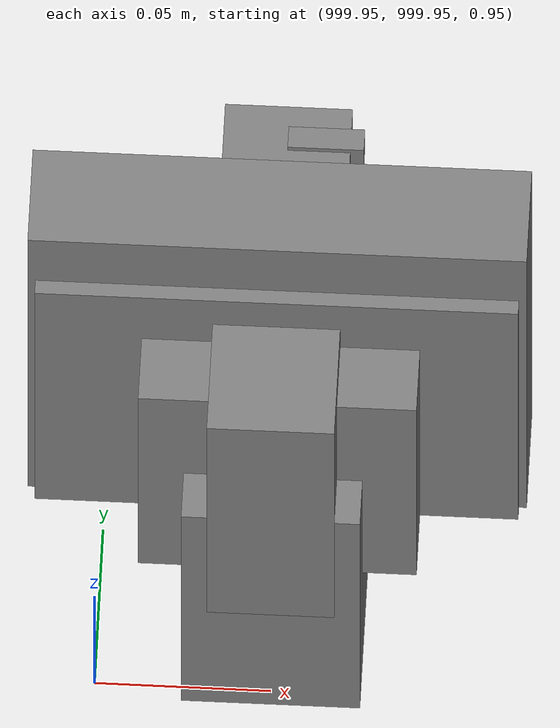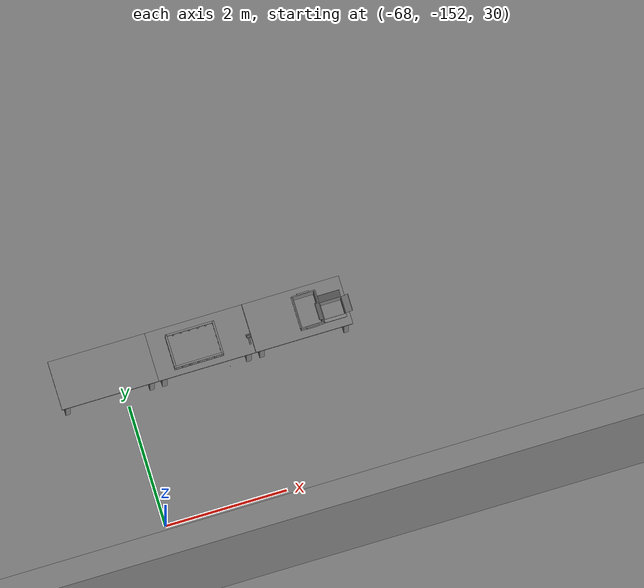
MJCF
<mujoco>
    <option gravity="0.000000000 0.000000000 -9.810000420" timestep="0.0049999999" integrator="implicitfast" density="1.225" viscosity="1.8000001e-05" noslip_iterations="10" iterations="100" sdf_iterations="50">
        <flag multiccd="disable"/>
    </option>
    <size memory="1000M"/>
    <compiler coordinate="local"/>
    <worldbody>
        <light cutoff="30" pos="0 1 1" dir="0 -1 -2"/>
        <light cutoff="30" pos="0 -1 1" dir="0 1 -2"/>
        <body pos="1000.000000000 1000.000000000 1.000000000" euler="0.000011953 0.000005123 -179.999984741" name="openloong_gripper_2f85_fix_base_usda_intel_box">
            <geom contype="1" conaffinity="1" density="1000" type="box" material="" rgba="0.500000000 0.500000000 0.500000000 1.000000000" solimp="0.899999976 0.949999988 0.001000000" friction="1.000000000 0.005000000 0.000100000" solref="0.020000000 1.000000000" margin="0" condim="3" group="0" pos="0.000000000 -0.000067139 0.000082284" quat="0.707106709 0.000000225 0.000000253 0.707106650" size="0.052800003 0.025300000 0.052800003" name="openloong_gripper_2f85_fix_base_usda_geom_028595FA_B960_4434_9718_BBE9CF19BB4A"/>
            <freejoint name="openloong_gripper_2f85_fix_base_usda_intel_box_joint"/>
            <site size="0.005000000 0.005000000 0.005000000" rgba="0.500000000 0.500000000 0.500000000 1.000000000" pos="0.000000000 0.000000000 0.000000000" quat="0.999961913 0.008726500 0.000000000 0.000000000" group="0" type="sphere" name="openloong_gripper_2f85_fix_base_usda_intel_boxsite"/>
        </body>
        <body pos="1000.000000000 1000.000000000 1.000000000" euler="0.000000000 0.000000000 180.000000000" name="openloong_gripper_2f85_fix_base_usda_wifi_box">
            <geom contype="1" conaffinity="1" density="1000" type="box" material="" rgba="0.500000000 0.500000000 0.500000000 1.000000000" solimp="0.899999976 0.949999988 0.001000000" friction="1.000000000 0.005000000 0.000100000" solref="0.020000000 1.000000000" margin="0" condim="3" group="0" pos="0.000000000 0.000000000 0.058978677" quat="0.000000000 0.000000047 0.000000000 1.000000000" size="0.068499997 0.018999999 0.059000000" name="openloong_gripper_2f85_fix_base_usda_geom_68BC1AEA_4498_43AB_B6B9_C622CF29A88A"/>
            <freejoint name="openloong_gripper_2f85_fix_base_usda_wifi_box_joint"/>
            <site size="0.005000000 0.005000000 0.005000000" rgba="0.500000000 0.500000000 0.500000000 1.000000000" pos="0.000000000 0.000000000 0.000000000" quat="0.999961913 0.008726500 0.000000000 0.000000000" group="0" type="sphere" name="openloong_gripper_2f85_fix_base_usda_wifi_boxsite"/>
        </body>
        <body pos="1000.000000000 1000.000000000 1.000000000" euler="0.000000000 0.000000000 180.000000000" name="openloong_gripper_2f85_fix_base_usda_cpu_fan">
            <geom contype="1" conaffinity="1" density="1000" type="box" material="" rgba="0.500000000 0.500000000 0.500000000 1.000000000" solimp="0.899999976 0.949999988 0.001000000" friction="1.000000000 0.005000000 0.000100000" solref="0.020000000 1.000000000" margin="0" condim="3" group="0" pos="0.000000000 0.000000000 0.070034981" quat="0.000000000 0.000000000 0.000000000 1.000000000" size="0.070700005 0.014699999 0.070700005" name="openloong_gripper_2f85_fix_base_usda_geom_0ED511C3_EB9A_4F50_9CC0_E1EF71EF05A9"/>
            <freejoint name="openloong_gripper_2f85_fix_base_usda_cpu_fan_joint"/>
            <site size="0.005000000 0.005000000 0.005000000" rgba="0.500000000 0.500000000 0.500000000 1.000000000" pos="0.000000000 0.000000000 0.000000000" quat="0.999961913 0.008726535 0.000000000 0.000000000" group="0" type="sphere" name="openloong_gripper_2f85_fix_base_usda_cpu_fancsite"/>
        </body>
        <body pos="1000.000000000 1000.000000000 1.000000000" euler="0.000000000 0.000000000 180.000000000" name="openloong_gripper_2f85_fix_base_usda_battery_01">
            <geom contype="1" conaffinity="1" density="1000" type="box" material="" rgba="0.500000000 0.500000000 0.500000000 1.000000000" solimp="0.899999976 0.949999988 0.001000000" friction="1.000000000 0.005000000 0.000100000" solref="0.020000000 1.000000000" margin="0" condim="3" group="0" pos="-0.011123657 -0.041940309 0.101691343" quat="1.000000000 0.000000000 0.000000000 0.000000000" size="0.010800000 0.003375000 0.004725000" name="openloong_gripper_2f85_fix_base_usda_geom_67DF7FAB_CD69_493D_9CA7_0DB8A246394A"/>
            <geom contype="1" conaffinity="1" density="1000" type="box" material="" rgba="0.500000000 0.500000000 0.500000000 1.000000000" solimp="0.899999976 0.949999988 0.001000000" friction="1.000000000 0.005000000 0.000100000" solref="0.020000000 1.000000000" margin="0" condim="3" group="0" pos="-0.010876465 -0.044247437 0.047066893" quat="0.998702705 -0.050920475 0.000000000 0.000000000" size="0.009450001 0.002700000 0.024975000" name="openloong_gripper_2f85_fix_base_usda_geom_8C90D920_45DF_4E12_937E_FC7C6B19257A"/>
            <geom contype="1" conaffinity="1" density="1000" type="box" material="" rgba="0.500000000 0.500000000 0.500000000 1.000000000" solimp="0.899999976 0.949999988 0.001000000" friction="1.000000000 0.005000000 0.000100000" solref="0.020000000 1.000000000" margin="0" condim="3" group="0" pos="-0.001235962 -0.000659180 0.047381196" quat="1.000000000 0.000000000 0.000000000 0.000000000" size="0.039420001 0.039150000 0.047250003" name="openloong_gripper_2f85_fix_base_usda_geom_DB84ECA6_1B1B_4C50_8BAB_A4E483B2B003"/>
            <geom contype="1" conaffinity="1" density="1000" type="box" material="" rgba="0.500000000 0.500000000 0.500000000 1.000000000" solimp="0.899999976 0.949999988 0.001000000" friction="1.000000000 0.005000000 0.000100000" solref="0.020000000 1.000000000" margin="0" condim="3" group="0" pos="-0.010876465 -0.039138794 0.009851727" quat="1.000000000 0.000000000 0.000000000 0.000000000" size="0.009450001 0.010800000 0.013500000" name="openloong_gripper_2f85_fix_base_usda_geom_F82D2DAD_322F_4C73_B22D_55CCA338E19C"/>
            <geom contype="1" conaffinity="1" density="1000" type="box" material="" rgba="0.500000000 0.500000000 0.500000000 1.000000000" solimp="0.899999976 0.949999988 0.001000000" friction="1.000000000 0.005000000 0.000100000" solref="0.020000000 1.000000000" margin="0" condim="3" group="0" pos="-0.010876465 -0.041528322 0.071508206" quat="1.000000000 0.000000000 0.000000000 0.000000000" size="0.009450001 0.002700000 0.027000001" name="openloong_gripper_2f85_fix_base_usda_geom_2DD188D8_8299_4808_ADEA_18A42ED6E5B7"/>
            <freejoint name="openloong_gripper_2f85_fix_base_usda_battery_01_joint"/>
            <site size="0.005000000 0.005000000 0.005000000" rgba="0.500000000 0.500000000 0.500000000 1.000000000" pos="0.000000000 0.000000000 0.000000000" quat="0.999961913 0.008726500 0.000000000 0.000000000" group="0" type="sphere" name="openloong_gripper_2f85_fix_base_usda_battery_01site"/>
        </body>
        <body pos="1000.000000000 999.999938965 1.000000000" euler="0.000000000 0.000000000 180.000000000" name="openloong_gripper_2f85_fix_base_usda_intelcore_i5">
            <geom contype="1" conaffinity="1" density="1000" type="box" material="" rgba="0.500000000 0.500000000 0.500000000 1.000000000" solimp="0.899999976 0.949999988 0.001000000" friction="1.000000000 0.005000000 0.000100000" solref="0.020000000 1.000000000" margin="0" condim="3" group="0" pos="0.000000000 0.000000000 0.051722717" quat="0.707106709 0.000000000 0.000000000 -0.707106769" size="0.052800000 0.018080002 0.052800000" name="openloong_gripper_2f85_fix_base_usda_geom_80DF3C99_9C17_4527_B5A9_3B303E156B97"/>
            <freejoint name="openloong_gripper_2f85_fix_base_usda_intelcore_i5_joint"/>
            <site size="0.005000000 0.005000000 0.005000000" rgba="0.500000000 0.500000000 0.500000000 1.000000000" pos="0.000000000 0.000000000 0.000000000" quat="0.999961913 0.008726534 0.000000000 0.000000000" group="0" type="sphere" name="openloong_gripper_2f85_fix_base_usda_intelcore_i5site"/>
        </body>
        <body pos="-65.855972290 -148.868896484 31.169614792" euler="-158.282546997 -80.667945862 -14.298255920" mocap="true" name="spotlight1_SpotLight"/>
        <body pos="-66.057823181 -149.180892944 31.169105530" euler="94.332489014 24.379175186 -79.895729065" mocap="true" name="spotlight2_SpotLight"/>
        <body pos="-66.336219788 -149.637802124 31.169216156" euler="41.773750305 35.313121796 -174.925369263" mocap="true" name="spotlight4_SpotLight"/>
        <body pos="-64.866622925 -149.383972168 30.183746338" euler="89.999984741 89.999946594 0.000000000" name="openloong_gripper_2f85_fix_base_usda_bluebox_01">
            <geom contype="1" conaffinity="1" density="1000" type="box" material="" rgba="0.500000000 0.500000000 0.500000000 1.000000000" solimp="0.899999976 0.949999988 0.001000000" friction="1.000000000 0.005000000 0.000100000" solref="0.020000000 1.000000000" margin="0" condim="3" group="0" pos="0.276580811 0.187225342 0.000068665" quat="0.707106948 0.000077471 0.707106352 0.000077486" size="0.100000001 0.057999998 0.010000000" name="openloong_gripper_2f85_fix_base_usda_geom_B5CE2247_46BB_480D_95EC_7D6D182C00EB"/>
            <geom contype="1" conaffinity="1" density="1000" type="box" material="" rgba="0.500000000 0.500000000 0.500000000 1.000000000" solimp="0.899999976 0.949999988 0.001000000" friction="1.000000000 0.005000000 0.000100000" solref="0.020000000 1.000000000" margin="0" condim="3" group="0" pos="0.000000000 0.002883911 0.000000000" quat="0.999999881 0.000000000 0.000000000 0.000000000" size="0.254000008 0.003000000 0.172000006" name="openloong_gripper_2f85_fix_base_usda_geom_8FB9616C_54CC_48F5_B7F8_7E2C2C468D8C"/>
            <geom contype="1" conaffinity="1" density="1000" type="box" material="" rgba="0.500000000 0.500000000 0.500000000 1.000000000" solimp="0.899999976 0.949999988 0.001000000" friction="1.000000000 0.005000000 0.000100000" solref="0.020000000 1.000000000" margin="0" condim="3" group="0" pos="0.000000000 0.124874115 0.173484802" quat="0.999796331 0.020176515 -0.000000015 0.000000030" size="0.259999990 0.119999997 0.007000000" name="openloong_gripper_2f85_fix_base_usda_geom_759E0A63_99D0_4B1B_A3B4_5EA3CB94DA5D"/>
            <geom contype="1" conaffinity="1" density="1000" type="box" material="" rgba="0.500000000 0.500000000 0.500000000 1.000000000" solimp="0.899999976 0.949999988 0.001000000" friction="1.000000000 0.005000000 0.000100000" solref="0.020000000 1.000000000" margin="0" condim="3" group="0" pos="0.000000000 0.124874115 -0.173469543" quat="0.999796331 -0.020176545 -0.000000015 0.000000000" size="0.259999990 0.119999997 0.007000000" name="openloong_gripper_2f85_fix_base_usda_geom_954E1C5A_2602_4854_BFCA_33148D007C8E"/>
            <geom contype="1" conaffinity="1" density="1000" type="box" material="" rgba="0.500000000 0.500000000 0.500000000 1.000000000" solimp="0.899999976 0.949999988 0.001000000" friction="1.000000000 0.005000000 0.000100000" solref="0.020000000 1.000000000" margin="0" condim="3" group="0" pos="0.000000000 0.214008331 0.188980103" quat="0.999912977 0.013176724 0.000000015 0.000000000" size="0.259999990 0.029999999 0.012500000" name="openloong_gripper_2f85_fix_base_usda_geom_6747F7FB_58C3_4567_9DC4_9807D343EB09"/>
            <geom contype="1" conaffinity="1" density="1000" type="box" material="" rgba="0.500000000 0.500000000 0.500000000 1.000000000" solimp="0.899999976 0.949999988 0.001000000" friction="1.000000000 0.005000000 0.000100000" solref="0.020000000 1.000000000" margin="0" condim="3" group="0" pos="-0.258361816 0.125289917 0.001876831" quat="0.702796936 -0.020792112 0.710783124 0.020769298" size="0.189999998 0.119999997 0.009000000" name="openloong_gripper_2f85_fix_base_usda_geom_B624CA9A_9A79_4655_B5D9_797094B3534C"/>
            <geom contype="1" conaffinity="1" density="1000" type="box" material="" rgba="0.500000000 0.500000000 0.500000000 1.000000000" solimp="0.899999976 0.949999988 0.001000000" friction="1.000000000 0.005000000 0.000100000" solref="0.020000000 1.000000000" margin="0" condim="3" group="0" pos="0.000000000 0.214008331 -0.188980103" quat="0.999912977 -0.013176769 0.000000030 0.000000015" size="0.259999990 0.029999999 0.012500000" name="openloong_gripper_2f85_fix_base_usda_geom_37904CAA_4E61_495F_B7A8_EC4CBE5FEC36"/>
            <geom contype="1" conaffinity="1" density="1000" type="box" material="" rgba="0.500000000 0.500000000 0.500000000 1.000000000" solimp="0.899999976 0.949999988 0.001000000" friction="1.000000000 0.005000000 0.000100000" solref="0.020000000 1.000000000" margin="0" condim="3" group="0" pos="-0.276611328 0.187225342 0.000068665" quat="0.707106650 0.000077441 0.707106709 0.000077456" size="0.100000001 0.057999998 0.010000000" name="openloong_gripper_2f85_fix_base_usda_geom_25A3EE93_E05E_47AB_8F49_69446E9FF9CA"/>
            <geom contype="1" conaffinity="1" density="1000" type="box" material="" rgba="0.500000000 0.500000000 0.500000000 1.000000000" solimp="0.899999976 0.949999988 0.001000000" friction="1.000000000 0.005000000 0.000100000" solref="0.020000000 1.000000000" margin="0" condim="3" group="0" pos="0.258331299 0.125289917 0.001876831" quat="0.702851415 0.018856421 0.710823774 -0.019329369" size="0.189999998 0.119999997 0.009000000" name="openloong_gripper_2f85_fix_base_usda_geom_71997BC2_F3C8_48D2_9F5F_9B0E84F93501"/>
            <freejoint name="openloong_gripper_2f85_fix_base_usda_bluebox_01_joint"/>
            <site size="0.005000000 0.005000000 0.005000000" rgba="0.500000000 0.500000000 0.500000000 1.000000000" pos="0.000000000 0.000000000 0.000000000" quat="0.999961913 0.008726534 0.000000000 0.000000000" group="0" type="sphere" name="openloong_gripper_2f85_fix_base_usda_bluebox_01site"/>
        </body>
        <body pos="-64.496299744 -149.491867065 30.235729218" euler="0.000000000 0.000000000 89.999946594" name="openloong_gripper_2f85_fix_base_usda_cardboardbox_01">
            <geom contype="1" conaffinity="1" density="1000" type="box" material="" rgba="0.500000000 0.500000000 0.500000000 1.000000000" solimp="0.899999976 0.949999988 0.001000000" friction="1.000000000 0.005000000 0.000100000" solref="0.020000000 1.000000000" margin="0" condim="3" group="0" pos="-0.003166199 -0.004086494 0.005052090" quat="1.000000000 0.000000000 0.000000000 0.000000000" size="0.142499998 0.177500010 0.005000000" name="openloong_gripper_2f85_fix_base_usda_geom_401D0967_E669_4467_865E_E52B418C8657"/>
            <geom contype="1" conaffinity="1" density="1000" type="box" material="" rgba="0.500000000 0.500000000 0.500000000 1.000000000" solimp="0.899999976 0.949999988 0.001000000" friction="1.000000000 0.005000000 0.000100000" solref="0.020000000 1.000000000" margin="0" condim="3" group="0" pos="-0.003166199 0.170316696 0.150570869" quat="1.000000000 0.000000000 0.000000000 0.000000000" size="0.142499998 0.005000000 0.149999991" name="openloong_gripper_2f85_fix_base_usda_geom_61256C03_9523_4F62_B629_8B690615F337"/>
            <geom contype="1" conaffinity="1" density="1000" type="box" material="" rgba="0.500000000 0.500000000 0.500000000 1.000000000" solimp="0.899999976 0.949999988 0.001000000" friction="1.000000000 0.005000000 0.000100000" solref="0.020000000 1.000000000" margin="0" condim="3" group="0" pos="-0.147399902 -0.005307198 0.150570869" quat="1.000000000 0.000000000 0.000000000 0.000000000" size="0.005000000 0.177500010 0.149999991" name="openloong_gripper_2f85_fix_base_usda_geom_4F9EC4CF_D20A_4576_B749_1C1DF78BF53C"/>
            <geom contype="1" conaffinity="1" density="1000" type="box" material="" rgba="0.500000000 0.500000000 0.500000000 1.000000000" solimp="0.899999976 0.949999988 0.001000000" friction="1.000000000 0.005000000 0.000100000" solref="0.020000000 1.000000000" margin="0" condim="3" group="0" pos="0.140275955 -0.005307198 0.150570869" quat="1.000000000 0.000000000 0.000000000 0.000000000" size="0.005000000 0.177500010 0.149999991" name="openloong_gripper_2f85_fix_base_usda_geom_D51F66BB_EEF3_4830_B92C_9EC085E23126"/>
            <geom contype="1" conaffinity="1" density="1000" type="box" material="" rgba="0.500000000 0.500000000 0.500000000 1.000000000" solimp="0.899999976 0.949999988 0.001000000" friction="1.000000000 0.005000000 0.000100000" solref="0.020000000 1.000000000" margin="0" condim="3" group="0" pos="-0.003166199 -0.181550980 0.150570869" quat="1.000000000 0.000000000 0.000000000 0.000000000" size="0.142499998 0.005000000 0.149999991" name="openloong_gripper_2f85_fix_base_usda_geom_D0E68884_6C1C_4F34_868B_D0AC814EA1ED"/>
            <freejoint name="openloong_gripper_2f85_fix_base_usda_cardboardbox_01_joint"/>
            <site size="0.005000000 0.005000000 0.005000000" rgba="0.500000000 0.500000000 0.500000000 1.000000000" pos="0.000000000 0.000000000 0.000000000" quat="0.999961913 0.008726535 0.000000000 0.000000000" group="0" type="sphere" name="openloong_gripper_2f85_fix_base_usda_site_F4583515_A650_4098_8035_86351BC87DB2"/>
            <body pos="0.139160156 -0.004048347 0.301930904" euler="-179.999954224 49.383502960 179.999954224" name="openloong_gripper_2f85_fix_base_usda_A1_006">
                <geom contype="1" conaffinity="1" density="1000" type="box" material="" rgba="0.500000000 0.500000000 0.500000000 1.000000000" solimp="0.899999976 0.949999988 0.001000000" friction="1.000000000 0.005000000 0.000100000" solref="0.020000000 1.000000000" margin="0" condim="3" group="0" pos="-0.071587563 0.000009537 0.001745224" quat="0.999999881 0.000000000 0.000000000 0.000000000" size="0.071249999 0.179999992 0.002500000" name="openloong_gripper_2f85_fix_base_usda_geom_979DB6F3_98B7_4FA3_B0C6_F367FFC06899"/>
                <joint armature="0" stiffness="0.07" damping="0.0099999998" axis="0.000000 1.000000 0.000000" type="hinge" name="openloong_gripper_2f85_fix_base_usda_A1_006"/>
            </body>
            <body pos="-0.145902634 -0.004086494 0.301938057" euler="-180.000000000 -60.000011444 -180.000000000" name="openloong_gripper_2f85_fix_base_usda_A2_006">
                <geom contype="1" conaffinity="1" density="1000" type="box" material="" rgba="0.500000000 0.500000000 0.500000000 1.000000000" solimp="0.899999976 0.949999988 0.001000000" friction="1.000000000 0.005000000 0.000100000" solref="0.020000000 1.000000000" margin="0" condim="3" group="0" pos="0.071268082 0.000009537 0.002717972" quat="0.000002921 0.000000000 -0.000000030 0.999999881" size="0.071249999 0.179999992 0.002500000" name="openloong_gripper_2f85_fix_base_usda_geom_EF15539A_FCFD_4E68_91BA_59D5809CC0A2"/>
                <joint armature="0" stiffness="0.07" damping="0.0099999998" axis="0.000000 1.000000 0.000000" type="hinge" name="openloong_gripper_2f85_fix_base_usda_A2_006"/>
            </body>
            <body pos="-0.003385544 0.175991058 0.301930904" euler="-125.858116150 -0.000004561 0.000002331" name="openloong_gripper_2f85_fix_base_usda_B2_006">
                <geom contype="1" conaffinity="1" density="1000" type="box" material="" rgba="0.500000000 0.500000000 0.500000000 1.000000000" solimp="0.899999976 0.949999988 0.001000000" friction="1.000000000 0.005000000 0.000100000" solref="0.020000000 1.000000000" margin="0" condim="3" group="0" pos="0.000009537 -0.070939064 -0.002470016" quat="0.999614120 0.027776197 -0.000000015 0.000000030" size="0.137500003 0.064999998 0.005000000" name="openloong_gripper_2f85_fix_base_usda_geom_2E0D989F_F3C8_4B5E_A64D_35D353251476"/>
                <joint armature="0" stiffness="0.07" damping="0.0099999998" axis="1.000000 0.000000 0.000000" type="hinge" name="openloong_gripper_2f85_fix_base_usda_B2_006"/>
            </body>
            <body pos="-0.003385544 -0.184140205 0.301938057" euler="147.805557251 0.000000000 0.000000000" name="openloong_gripper_2f85_fix_base_usda_B1_006">
                <geom contype="1" conaffinity="1" density="1000" type="box" material="" rgba="0.500000000 0.500000000 0.500000000 1.000000000" solimp="0.899999976 0.949999988 0.001000000" friction="1.000000000 0.005000000 0.000100000" solref="0.020000000 1.000000000" margin="0" condim="3" group="0" pos="-0.000028610 0.070202351 -0.002703667" quat="0.999614179 -0.027776167 0.000000000 0.000000000" size="0.137500003 0.064999998 0.005000000" name="openloong_gripper_2f85_fix_base_usda_geom_7BF22C73_C5F5_400A_AD25_F03B69DCBEF8"/>
                <joint armature="0" stiffness="0.07" damping="0.0099999998" axis="1.000000 0.000000 0.000000" type="hinge" name="openloong_gripper_2f85_fix_base_usda_B1_006"/>
            </body>
        </body>
        <body pos="-65.882858276 -149.481979370 30.229999542" euler="-64.487716675 0.000000000 0.000000000" name="openloong_gripper_2f85_fix_base_usda_Barcode">
            <geom contype="1" conaffinity="1" density="1000" type="box" material="" rgba="0.500000000 0.500000000 0.500000000 1.000000000" solimp="0.899999976 0.949999988 0.001000000" friction="1.000000000 0.005000000 0.000100000" solref="0.020000000 1.000000000" margin="0" condim="3" group="0" pos="0.000000000 0.013038635 0.001419067" quat="0.000000000 0.000000000 0.000000000 1.000000119" size="0.034000002 0.010000000 0.017999999" name="openloong_gripper_2f85_fix_base_usda_geom_678DB86D_E971_463D_A5F2_FA621DC6CC4D"/>
            <geom contype="1" conaffinity="1" density="1000" type="box" material="" rgba="0.500000000 0.500000000 0.500000000 1.000000000" solimp="0.899999976 0.949999988 0.001000000" friction="1.000000000 0.005000000 0.000100000" solref="0.020000000 1.000000000" margin="0" condim="3" group="0" pos="0.000000000 -0.035301208 -0.007095337" quat="0.000000000 0.000000000 -0.043619365 0.999048233" size="0.028999999 0.010000000 0.020000000" name="openloong_gripper_2f85_fix_base_usda_geom_388A5906_39E4_4C39_828C_7D8F8D8440C2"/>
            <geom contype="1" conaffinity="1" density="1000" type="box" material="" rgba="0.500000000 0.500000000 0.500000000 1.000000000" solimp="0.899999976 0.949999988 0.001000000" friction="1.000000000 0.005000000 0.000100000" solref="0.020000000 1.000000000" margin="0" condim="3" group="0" pos="0.000000000 -0.043411255 -0.011749268" quat="0.922262907 0.386563420 0.000000000 0.000000000" size="0.026000001 0.010000000 0.020000000" name="openloong_gripper_2f85_fix_base_usda_geom_362D3E69_6770_4A6D_BD17_9DFE7CACDFA2"/>
            <geom contype="1" conaffinity="1" density="1000" type="box" material="" rgba="0.500000000 0.500000000 0.500000000 1.000000000" solimp="0.899999976 0.949999988 0.001000000" friction="1.000000000 0.005000000 0.000100000" solref="0.020000000 1.000000000" margin="0" condim="3" group="0" pos="0.000000000 -0.016967773 -0.031860352" quat="0.000000000 0.000000000 0.000000000 1.000000119" size="0.008000000 0.010000000 0.013000000" name="openloong_gripper_2f85_fix_base_usda_geom_D5C1D077_61A5_4550_B160_4B559D1D8EF1"/>
            <geom contype="1" conaffinity="1" density="1000" type="box" material="" rgba="0.500000000 0.500000000 0.500000000 1.000000000" solimp="0.899999976 0.949999988 0.001000000" friction="1.000000000 0.005000000 0.000100000" solref="0.020000000 1.000000000" margin="0" condim="3" group="0" pos="0.000000000 -0.001869202 0.000312805" quat="0.953716993 0.300705761 0.000000000 0.000000000" size="0.032000002 0.010000000 0.018999999" name="openloong_gripper_2f85_fix_base_usda_geom_9082965B_F1FC_4003_A012_8B1BCC949443"/>
            <geom contype="1" conaffinity="1" density="1000" type="box" material="" rgba="0.500000000 0.500000000 0.500000000 1.000000000" solimp="0.899999976 0.949999988 0.001000000" friction="1.000000000 0.005000000 0.000100000" solref="0.020000000 1.000000000" margin="0" condim="3" group="0" pos="0.000000000 -0.019531250 -0.003173828" quat="0.953716993 0.300705761 0.000000000 0.000000000" size="0.030999999 0.010000000 0.020000000" name="openloong_gripper_2f85_fix_base_usda_geom_64EEC982_2D33_453D_825F_C0D3645BC469"/>
            <geom contype="1" conaffinity="1" density="1000" type="box" material="" rgba="0.500000000 0.500000000 0.500000000 1.000000000" solimp="0.899999976 0.949999988 0.001000000" friction="1.000000000 0.005000000 0.000100000" solref="0.020000000 1.000000000" margin="0" condim="3" group="0" pos="0.000000000 -0.035301208 -0.007095337" quat="0.953716993 0.300705761 0.000000000 0.000000000" size="0.028999999 0.010000000 0.020000000" name="openloong_gripper_2f85_fix_base_usda_geom_97EDC65B_5984_4ADA_8756_7F4C56A81DA1"/>
            <geom contype="1" conaffinity="1" density="1000" type="box" material="" rgba="0.500000000 0.500000000 0.500000000 1.000000000" solimp="0.899999976 0.949999988 0.001000000" friction="1.000000000 0.005000000 0.000100000" solref="0.020000000 1.000000000" margin="0" condim="3" group="0" pos="0.000000000 -0.042617798 -0.071121216" quat="0.000000000 0.000000000 0.000000000 1.000000119" size="0.013000000 0.021000000 0.059999999" name="openloong_gripper_2f85_fix_base_usda_geom_D382836D_3C5B_47B5_8DE3_A3C6D3F9C829"/>
            <freejoint name="openloong_gripper_2f85_fix_base_usda_Barcode_joint"/>
            <site size="0.005000000 0.005000000 0.005000000" rgba="0.500000000 0.500000000 0.500000000 1.000000000" pos="0.000000000 0.000000000 0.000000000" quat="1.000000000 0.000000000 0.000000000 0.000000000" group="0" type="sphere" name="openloong_gripper_2f85_fix_base_usda_Barcode_site"/>
        </body>
        <body pos="-66.745018005 -149.392349243 30.184000015" euler="0.000000000 0.000000000 89.999946594" name="[22332158843988]_Basket_01">
            <geom contype="1" conaffinity="1" density="1000" type="box" material="" rgba="0.500000000 0.500000000 0.500000000 1.000000000" solimp="0.899999976 0.949999988 0.001000000" friction="1.000000000 0.005000000 0.000100000" solref="0.020000000 1.000000000" margin="0" condim="3" group="0" pos="-0.052425385 0.389207840 0.089787483" quat="0.707107008 0.000000000 0.000000000 0.707106411" size="0.014249999 0.014249999 0.059999999" name="[22332158843988]_geom_676E434B_6122_40B3_80D9_61505093E38E"/>
            <geom contype="1" conaffinity="1" density="1000" type="box" material="" rgba="0.500000000 0.500000000 0.500000000 1.000000000" solimp="0.899999976 0.949999988 0.001000000" friction="1.000000000 0.005000000 0.000100000" solref="0.020000000 1.000000000" margin="0" condim="3" group="0" pos="0.264015198 -0.133043289 0.089787483" quat="0.707107008 0.000000000 0.000000000 0.707106411" size="0.014249999 0.014249999 0.059999999" name="[22332158843988]_geom_812E3EBA_2825_4B95_BDC7_591F924D6FA5"/>
            <geom contype="1" conaffinity="1" density="1000" type="box" material="" rgba="0.500000000 0.500000000 0.500000000 1.000000000" solimp="0.899999976 0.949999988 0.001000000" friction="1.000000000 0.005000000 0.000100000" solref="0.020000000 1.000000000" margin="0" condim="3" group="0" pos="-0.264015198 -0.265548706 0.089793205" quat="0.707107008 0.000000000 0.000000000 0.707106411" size="0.014249999 0.014249999 0.059999999" name="[22332158843988]_geom_973CE7AD_05EC_4F37_934D_98DCB2C6881E"/>
            <geom contype="1" conaffinity="1" density="1000" type="box" material="" rgba="0.500000000 0.500000000 0.500000000 1.000000000" solimp="0.899999976 0.949999988 0.001000000" friction="1.000000000 0.005000000 0.000100000" solref="0.020000000 1.000000000" margin="0" condim="3" group="0" pos="-0.160263062 -0.389322281 0.089793205" quat="0.707107008 0.000000000 0.000000000 0.707106411" size="0.014249999 0.014249999 0.059999999" name="[22332158843988]_geom_5482068C_6781_490F_938E_1882184077FA"/>
            <geom contype="1" conaffinity="1" density="1000" type="box" material="" rgba="0.500000000 0.500000000 0.500000000 1.000000000" solimp="0.899999976 0.949999988 0.001000000" friction="1.000000000 0.005000000 0.000100000" solref="0.020000000 1.000000000" margin="0" condim="3" group="0" pos="0.162265778 -0.389322281 0.089787483" quat="0.707107008 0.000000000 0.000000000 0.707106411" size="0.014249999 0.014249999 0.059999999" name="[22332158843988]_geom_912E52EA_9E29_42FD_8506_47E739F27A42"/>
            <geom contype="1" conaffinity="1" density="1000" type="box" material="" rgba="0.500000000 0.500000000 0.500000000 1.000000000" solimp="0.899999976 0.949999988 0.001000000" friction="1.000000000 0.005000000 0.000100000" solref="0.020000000 1.000000000" margin="0" condim="3" group="0" pos="0.264015198 0.389207840 0.089787483" quat="0.707107008 0.000000000 0.000000000 0.707106411" size="0.014249999 0.014249999 0.059999999" name="[22332158843988]_geom_AE117FEC_B6A1_4D0F_AFBC_20CB347D2D03"/>
            <geom contype="1" conaffinity="1" density="1000" type="box" material="" rgba="0.500000000 0.500000000 0.500000000 1.000000000" solimp="0.899999976 0.949999988 0.001000000" friction="1.000000000 0.005000000 0.000100000" solref="0.020000000 1.000000000" margin="0" condim="3" group="0" pos="-0.264015198 -0.133043289 0.089793205" quat="0.707107008 0.000000000 0.000000000 0.707106411" size="0.014249999 0.014249999 0.059999999" name="[22332158843988]_geom_7795F237_D150_46AF_89E9_9638565B3BB6"/>
            <geom contype="1" conaffinity="1" density="1000" type="box" material="" rgba="0.500000000 0.500000000 0.500000000 1.000000000" solimp="0.899999976 0.949999988 0.001000000" friction="1.000000000 0.005000000 0.000100000" solref="0.020000000 1.000000000" margin="0" condim="3" group="0" pos="-0.264026642 0.269256592 0.089793205" quat="0.707107008 0.000000000 0.000000000 0.707106411" size="0.014249999 0.014249999 0.059999999" name="[22332158843988]_geom_DD27970A_591F_424C_A682_25D5F86E3ABB"/>
            <geom contype="1" conaffinity="1" density="1000" type="box" material="" rgba="0.500000000 0.500000000 0.500000000 1.000000000" solimp="0.899999976 0.949999988 0.001000000" friction="1.000000000 0.005000000 0.000100000" solref="0.020000000 1.000000000" margin="0" condim="3" group="0" pos="0.054462433 0.389207840 0.089787483" quat="0.707107008 0.000000000 0.000000000 0.707106411" size="0.014249999 0.014249999 0.059999999" name="[22332158843988]_geom_9E661987_BF81_4B5D_A63C_406AE4443B33"/>
            <geom contype="1" conaffinity="1" density="1000" type="box" material="" rgba="0.500000000 0.500000000 0.500000000 1.000000000" solimp="0.899999976 0.949999988 0.001000000" friction="1.000000000 0.005000000 0.000100000" solref="0.020000000 1.000000000" margin="0" condim="3" group="0" pos="0.054462433 -0.389322281 0.089787483" quat="0.707107008 0.000000000 0.000000000 0.707106411" size="0.014249999 0.014249999 0.059999999" name="[22332158843988]_geom_FE30D340_29A7_4702_A8CC_F1C085C194CC"/>
            <geom contype="1" conaffinity="1" density="1000" type="box" material="" rgba="0.500000000 0.500000000 0.500000000 1.000000000" solimp="0.899999976 0.949999988 0.001000000" friction="1.000000000 0.005000000 0.000100000" solref="0.020000000 1.000000000" margin="0" condim="3" group="0" pos="0.264015198 0.269256592 0.089793205" quat="0.707107008 0.000000000 0.000000000 0.707106411" size="0.014249999 0.014249999 0.059999999" name="[22332158843988]_geom_D3486AC1_80D3_4292_9B70_F197E6DB02F5"/>
            <geom contype="1" conaffinity="1" density="1000" type="box" material="" rgba="0.500000000 0.500000000 0.500000000 1.000000000" solimp="0.899999976 0.949999988 0.001000000" friction="1.000000000 0.005000000 0.000100000" solref="0.020000000 1.000000000" margin="0" condim="3" group="0" pos="0.264015198 -0.389322281 0.089787483" quat="0.707107008 0.000000000 0.000000000 0.707106411" size="0.014249999 0.014249999 0.059999999" name="[22332158843988]_geom_CC5BFC0C_3AED_48DA_8736_BEB80E0CBBC7"/>
            <geom contype="1" conaffinity="1" density="1000" type="box" material="" rgba="0.500000000 0.500000000 0.500000000 1.000000000" solimp="0.899999976 0.949999988 0.001000000" friction="1.000000000 0.005000000 0.000100000" solref="0.020000000 1.000000000" margin="0" condim="3" group="0" pos="0.000000000 0.000000000 0.015998840" quat="0.707107008 0.000000000 0.000000000 0.707106411" size="0.403499991 0.279000014 0.015750000" name="[22332158843988]_geom_98C5646E_4DDC_49FC_8F8A_1DE677A5150C"/>
            <geom contype="1" conaffinity="1" density="1000" type="box" material="" rgba="0.500000000 0.500000000 0.500000000 1.000000000" solimp="0.899999976 0.949999988 0.001000000" friction="1.000000000 0.005000000 0.000100000" solref="0.020000000 1.000000000" margin="0" condim="3" group="0" pos="0.000000000 -0.389476776 0.163619041" quat="0.707107008 0.000000000 0.000000000 0.707106411" size="0.015000000 0.277500004 0.015750000" name="[22332158843988]_geom_A7EC8254_F340_43DF_B577_39FAF006C41B"/>
            <geom contype="1" conaffinity="1" density="1000" type="box" material="" rgba="0.500000000 0.500000000 0.500000000 1.000000000" solimp="0.899999976 0.949999988 0.001000000" friction="1.000000000 0.005000000 0.000100000" solref="0.020000000 1.000000000" margin="0" condim="3" group="0" pos="0.162265778 0.389207840 0.089787483" quat="0.707107008 0.000000000 0.000000000 0.707106411" size="0.014249999 0.014249999 0.059999999" name="[22332158843988]_geom_FAF167DC_C93B_41B8_A442_3C29FA0D630E"/>
            <geom contype="1" conaffinity="1" density="1000" type="box" material="" rgba="0.500000000 0.500000000 0.500000000 1.000000000" solimp="0.899999976 0.949999988 0.001000000" friction="1.000000000 0.005000000 0.000100000" solref="0.020000000 1.000000000" margin="0" condim="3" group="0" pos="0.000000000 0.389471054 0.163619041" quat="0.707107008 0.000000000 0.000000000 0.707106411" size="0.015000000 0.277500004 0.015750000" name="[22332158843988]_geom_EC5E2104_9B5B_4AD9_962A_495CF60B00A2"/>
            <geom contype="1" conaffinity="1" density="1000" type="box" material="" rgba="0.500000000 0.500000000 0.500000000 1.000000000" solimp="0.899999976 0.949999988 0.001000000" friction="1.000000000 0.005000000 0.000100000" solref="0.020000000 1.000000000" margin="0" condim="3" group="0" pos="-0.263511658 0.000000000 0.163619041" quat="0.707107008 0.000000000 0.000000000 0.707106411" size="0.403499991 0.015000000 0.015750000" name="[22332158843988]_geom_E64FA5BA_4C2D_425D_A833_112D131A7DE2"/>
            <geom contype="1" conaffinity="1" density="1000" type="box" material="" rgba="0.500000000 0.500000000 0.500000000 1.000000000" solimp="0.899999976 0.949999988 0.001000000" friction="1.000000000 0.005000000 0.000100000" solref="0.020000000 1.000000000" margin="0" condim="3" group="0" pos="-0.264015198 0.141334534 0.089793205" quat="0.707107008 0.000000000 0.000000000 0.707106411" size="0.014249999 0.014249999 0.059999999" name="[22332158843988]_geom_4FEC7253_C262_43D2_A144_DC1C5D82188B"/>
            <geom contype="1" conaffinity="1" density="1000" type="box" material="" rgba="0.500000000 0.500000000 0.500000000 1.000000000" solimp="0.899999976 0.949999988 0.001000000" friction="1.000000000 0.005000000 0.000100000" solref="0.020000000 1.000000000" margin="0" condim="3" group="0" pos="0.264015198 -0.265548706 0.089787483" quat="0.707107008 0.000000000 0.000000000 0.707106411" size="0.014249999 0.014249999 0.059999999" name="[22332158843988]_geom_E4D6E69A_62D9_4F4B_968D_89D3891699C4"/>
            <geom contype="1" conaffinity="1" density="1000" type="box" material="" rgba="0.500000000 0.500000000 0.500000000 1.000000000" solimp="0.899999976 0.949999988 0.001000000" friction="1.000000000 0.005000000 0.000100000" solref="0.020000000 1.000000000" margin="0" condim="3" group="0" pos="-0.160263062 0.389207840 0.089787483" quat="0.707107008 0.000000000 0.000000000 0.707106411" size="0.014249999 0.014249999 0.059999999" name="[22332158843988]_geom_CDA0E602_F814_4D28_B610_DEE4166B248B"/>
            <geom contype="1" conaffinity="1" density="1000" type="box" material="" rgba="0.500000000 0.500000000 0.500000000 1.000000000" solimp="0.899999976 0.949999988 0.001000000" friction="1.000000000 0.005000000 0.000100000" solref="0.020000000 1.000000000" margin="0" condim="3" group="0" pos="-0.052425385 -0.389322281 0.089787483" quat="0.707107008 0.000000000 0.000000000 0.707106411" size="0.014249999 0.014249999 0.059999999" name="[22332158843988]_geom_19998FA1_81BC_4B99_A389_1D864660A92E"/>
            <geom contype="1" conaffinity="1" density="1000" type="box" material="" rgba="0.500000000 0.500000000 0.500000000 1.000000000" solimp="0.899999976 0.949999988 0.001000000" friction="1.000000000 0.005000000 0.000100000" solref="0.020000000 1.000000000" margin="0" condim="3" group="0" pos="-0.264026642 -0.389322281 0.089793205" quat="0.707107008 0.000000000 0.000000000 0.707106411" size="0.014249999 0.014249999 0.059999999" name="[22332158843988]_geom_3DADC0E2_36B0_43C8_8936_B7BD25724632"/>
            <geom contype="1" conaffinity="1" density="1000" type="box" material="" rgba="0.500000000 0.500000000 0.500000000 1.000000000" solimp="0.899999976 0.949999988 0.001000000" friction="1.000000000 0.005000000 0.000100000" solref="0.020000000 1.000000000" margin="0" condim="3" group="0" pos="0.264015198 0.141334534 0.089787483" quat="0.707107008 0.000000000 0.000000000 0.707106411" size="0.014249999 0.014249999 0.059999999" name="[22332158843988]_geom_C09AC2D0_0D61_4CEE_A898_B94B1C36903C"/>
            <geom contype="1" conaffinity="1" density="1000" type="box" material="" rgba="0.500000000 0.500000000 0.500000000 1.000000000" solimp="0.899999976 0.949999988 0.001000000" friction="1.000000000 0.005000000 0.000100000" solref="0.020000000 1.000000000" margin="0" condim="3" group="0" pos="-0.264015198 0.389207840 0.089793205" quat="0.707107008 0.000000000 0.000000000 0.707106411" size="0.014249999 0.014249999 0.059999999" name="[22332158843988]_geom_CF8CC479_164B_47E7_A355_546D5C59CAE4"/>
            <geom contype="1" conaffinity="1" density="1000" type="box" material="" rgba="0.500000000 0.500000000 0.500000000 1.000000000" solimp="0.899999976 0.949999988 0.001000000" friction="1.000000000 0.005000000 0.000100000" solref="0.020000000 1.000000000" margin="0" condim="3" group="0" pos="0.264015198 0.004480362 0.089787483" quat="0.707107008 0.000000000 0.000000000 0.707106411" size="0.014249999 0.014249999 0.059999999" name="[22332158843988]_geom_4417E811_729B_4EFB_9106_9497BB925025"/>
            <geom contype="1" conaffinity="1" density="1000" type="box" material="" rgba="0.500000000 0.500000000 0.500000000 1.000000000" solimp="0.899999976 0.949999988 0.001000000" friction="1.000000000 0.005000000 0.000100000" solref="0.020000000 1.000000000" margin="0" condim="3" group="0" pos="0.263694763 -0.000011444 0.163619041" quat="0.707107008 0.000000000 0.000000000 0.707106411" size="0.403499991 0.015000000 0.015750000" name="[22332158843988]_geom_2AA5D45B_36D3_429B_BA8E_803A6ADF2826"/>
            <geom contype="1" conaffinity="1" density="1000" type="box" material="" rgba="0.500000000 0.500000000 0.500000000 1.000000000" solimp="0.899999976 0.949999988 0.001000000" friction="1.000000000 0.005000000 0.000100000" solref="0.020000000 1.000000000" margin="0" condim="3" group="0" pos="-0.264015198 0.004480362 0.089793205" quat="0.707107008 0.000000000 0.000000000 0.707106411" size="0.014249999 0.014249999 0.059999999" name="[22332158843988]_geom_42B7E365_A3A3_479E_8FDE_9BE79B40ECE4"/>
            <freejoint name="[22332158843988]_joint_95E59B95_F1CE_47EA_A0EB_725ACD670712"/>
        </body>
        <body pos="0.000000000 0.000000000 0.000000000" euler="0.000000000 0.000000000 0.000000000" name="Static Objects_Static Objects">
            <geom contype="1" conaffinity="1" density="1000" type="box" material="" rgba="0.500000000 0.500000000 0.500000000 1.000000000" solimp="0.899999976 0.949999988 0.001000000" friction="1.000000000 0.005000000 0.000100000" solref="0.020000000 1.000000000" margin="0" condim="3" group="0" pos="-67.544113159 -149.365814209 29.727830887" quat="0.500000417 0.499999970 0.499999553 0.499999970" size="0.381000012 0.319999993 0.041000001" name="Static Objects_geom_44B48CBB_64F3_487B_BCF6_523228B276FB"/>
            <geom contype="1" conaffinity="1" density="1000" type="box" material="" rgba="0.500000000 0.500000000 0.500000000 1.000000000" solimp="0.899999976 0.949999988 0.001000000" friction="1.000000000 0.005000000 0.000100000" solref="0.020000000 1.000000000" margin="0" condim="3" group="0" pos="-68.239501953 -149.365814209 30.086868286" quat="0.500000417 0.499999970 0.499999553 0.499999970" size="0.370999992 0.039500002 0.745000005" name="Static Objects_geom_1CF018D5_8B36_457C_ACEA_FB4D88519C02"/>
            <geom contype="1" conaffinity="1" density="1000" type="box" material="" rgba="0.500000000 0.500000000 0.500000000 1.000000000" solimp="0.899999976 0.949999988 0.001000000" friction="1.000000000 0.005000000 0.000100000" solref="0.020000000 1.000000000" margin="0" condim="3" group="0" pos="-68.239501953 -149.365814209 30.147235870" quat="0.500000417 0.499999970 0.499999553 0.499999970" size="0.400000006 0.022000000 0.800000012" name="Static Objects_geom_160610D3_8113_4656_B3CF_2F7ED1A3FF87"/>
            <geom contype="1" conaffinity="1" density="1000" type="box" material="" rgba="0.500000000 0.500000000 0.500000000 1.000000000" solimp="0.899999976 0.949999988 0.001000000" friction="1.000000000 0.005000000 0.000100000" solref="0.020000000 1.000000000" margin="0" condim="3" group="0" pos="-68.934890747 -149.365814209 29.727830887" quat="0.500000417 0.499999970 0.499999553 0.499999970" size="0.381000012 0.319999993 0.041000001" name="Static Objects_geom_9F16A4E9_FFDB_49AC_A48F_0F0100E94F29"/>
            <geom contype="1" conaffinity="1" density="1000" type="box" material="" rgba="0.500000000 0.500000000 0.500000000 1.000000000" solimp="0.899999976 0.949999988 0.001000000" friction="1.000000000 0.005000000 0.000100000" solref="0.020000000 1.000000000" margin="0" condim="3" group="0" pos="-68.239501953 -149.365814209 29.561563492" quat="0.500000417 0.499999970 0.499999553 0.499999970" size="0.020000000 0.022000000 0.660000026" name="Static Objects_geom_93234EB6_D3DF_4BF7_95B8_CFB3BD0B1A2E"/>
            <geom contype="1" conaffinity="1" density="1000" type="box" material="" rgba="0.500000000 0.500000000 0.500000000 1.000000000" solimp="0.899999976 0.949999988 0.001000000" friction="1.000000000 0.005000000 0.000100000" solref="0.020000000 1.000000000" margin="0" condim="3" group="0" pos="-65.945671082 -149.365814209 29.727830887" quat="0.500000417 0.499999970 0.499999553 0.499999970" size="0.381000012 0.319999993 0.041000001" name="Static Objects_geom_AC37FC90_E88D_462B_9EA3_1CB53B9AED4C"/>
            <geom contype="1" conaffinity="1" density="1000" type="box" material="" rgba="0.500000000 0.500000000 0.500000000 1.000000000" solimp="0.899999976 0.949999988 0.001000000" friction="1.000000000 0.005000000 0.000100000" solref="0.020000000 1.000000000" margin="0" condim="3" group="0" pos="-66.641059875 -149.365814209 30.086868286" quat="0.500000417 0.499999970 0.499999553 0.499999970" size="0.370999992 0.039500002 0.745000005" name="Static Objects_geom_F80CC61D_852C_47BC_B0ED_EFF433FAAB50"/>
            <geom contype="1" conaffinity="1" density="1000" type="box" material="" rgba="0.500000000 0.500000000 0.500000000 1.000000000" solimp="0.899999976 0.949999988 0.001000000" friction="1.000000000 0.005000000 0.000100000" solref="0.020000000 1.000000000" margin="0" condim="3" group="0" pos="-66.641059875 -149.365814209 30.147235870" quat="0.500000417 0.499999970 0.499999553 0.499999970" size="0.400000006 0.022000000 0.800000012" name="Static Objects_geom_073587F3_4086_4EB5_92A0_DD8BA4E307EE"/>
            <geom contype="1" conaffinity="1" density="1000" type="box" material="" rgba="0.500000000 0.500000000 0.500000000 1.000000000" solimp="0.899999976 0.949999988 0.001000000" friction="1.000000000 0.005000000 0.000100000" solref="0.020000000 1.000000000" margin="0" condim="3" group="0" pos="-67.336448669 -149.365814209 29.727830887" quat="0.500000417 0.499999970 0.499999553 0.499999970" size="0.381000012 0.319999993 0.041000001" name="Static Objects_geom_DE11328A_71B4_4E3E_8A14_5225F5728330"/>
            <geom contype="1" conaffinity="1" density="1000" type="box" material="" rgba="0.500000000 0.500000000 0.500000000 1.000000000" solimp="0.899999976 0.949999988 0.001000000" friction="1.000000000 0.005000000 0.000100000" solref="0.020000000 1.000000000" margin="0" condim="3" group="0" pos="-66.641059875 -149.365814209 29.561563492" quat="0.500000417 0.499999970 0.499999553 0.499999970" size="0.020000000 0.022000000 0.660000026" name="Static Objects_geom_3CE83544_E37E_43A1_886F_4A9FF273BED5"/>
            <geom contype="1" conaffinity="1" density="1000" type="box" material="" rgba="0.500000000 0.500000000 0.500000000 1.000000000" solimp="0.899999976 0.949999988 0.001000000" friction="1.000000000 0.005000000 0.000100000" solref="0.020000000 1.000000000" margin="0" condim="3" group="0" pos="-64.338577271 -149.365814209 29.727830887" quat="0.500000417 0.499999970 0.499999553 0.499999970" size="0.381000012 0.319999993 0.041000001" name="Static Objects_geom_95C28D1D_C85E_4530_A76D_BB2AEE3BF3C4"/>
            <geom contype="1" conaffinity="1" density="1000" type="box" material="" rgba="0.500000000 0.500000000 0.500000000 1.000000000" solimp="0.899999976 0.949999988 0.001000000" friction="1.000000000 0.005000000 0.000100000" solref="0.020000000 1.000000000" margin="0" condim="3" group="0" pos="-65.033966064 -149.365814209 30.086868286" quat="0.500000417 0.499999970 0.499999553 0.499999970" size="0.370999992 0.039500002 0.745000005" name="Static Objects_geom_86336EF0_5A03_4E00_9518_DC553537652E"/>
            <geom contype="1" conaffinity="1" density="1000" type="box" material="" rgba="0.500000000 0.500000000 0.500000000 1.000000000" solimp="0.899999976 0.949999988 0.001000000" friction="1.000000000 0.005000000 0.000100000" solref="0.020000000 1.000000000" margin="0" condim="3" group="0" pos="-65.033966064 -149.365814209 30.147235870" quat="0.500000417 0.499999970 0.499999553 0.499999970" size="0.400000006 0.022000000 0.800000012" name="Static Objects_geom_F07DA703_EFDD_46AA_BE62_49E932ECB27D"/>
            <geom contype="1" conaffinity="1" density="1000" type="box" material="" rgba="0.500000000 0.500000000 0.500000000 1.000000000" solimp="0.899999976 0.949999988 0.001000000" friction="1.000000000 0.005000000 0.000100000" solref="0.020000000 1.000000000" margin="0" condim="3" group="0" pos="-65.729354858 -149.365814209 29.727830887" quat="0.500000417 0.499999970 0.499999553 0.499999970" size="0.381000012 0.319999993 0.041000001" name="Static Objects_geom_2564CAD1_EAD3_4553_B537_BA94A4C089EE"/>
            <geom contype="1" conaffinity="1" density="1000" type="box" material="" rgba="0.500000000 0.500000000 0.500000000 1.000000000" solimp="0.899999976 0.949999988 0.001000000" friction="1.000000000 0.005000000 0.000100000" solref="0.020000000 1.000000000" margin="0" condim="3" group="0" pos="-65.033966064 -149.365814209 29.561563492" quat="0.500000417 0.499999970 0.499999553 0.499999970" size="0.020000000 0.022000000 0.660000026" name="Static Objects_geom_0034C2CD_E5E8_41AA_8FAC_C17A9243ECB4"/>
            <geom contype="1" conaffinity="1" density="1000" type="box" material="" rgba="0.500000000 0.500000000 0.500000000 1.000000000" solimp="0.899999976 0.949999988 0.001000000" friction="1.000000000 0.005000000 0.000100000" solref="0.020000000 1.000000000" margin="0" condim="3" group="0" pos="-61.754566193 -137.853729248 33.906845093" quat="0.707107067 0.000000000 0.000000000 0.707106471" size="0.759999990 0.759999990 4.500000000" name="Static Objects_geom_6FD808D4_912D_43B0_B985_919FC6CE22EF"/>
            <geom contype="1" conaffinity="1" density="1000" type="box" material="" rgba="0.500000000 0.500000000 0.500000000 1.000000000" solimp="0.899999976 0.949999988 0.001000000" friction="1.000000000 0.005000000 0.000100000" solref="0.020000000 1.000000000" margin="0" condim="3" group="0" pos="-57.511135101 -144.927108765 31.707921982" quat="1.000000000 0.000000000 0.000000000 0.000000000" size="0.200000003 8.000000000 2.299999952" name="Static Objects_geom_63BF9817_AFE3_475B_BB30_F17534A7C320"/>
            <geom contype="1" conaffinity="1" density="1000" type="box" material="" rgba="0.500000000 0.500000000 0.500000000 1.000000000" solimp="0.899999976 0.949999988 0.001000000" friction="1.000000000 0.005000000 0.000100000" solref="0.020000000 1.000000000" margin="0" condim="3" group="0" pos="-80.517646790 -157.574050903 31.688196182" quat="0.707107067 0.000000000 0.000000000 0.707106471" size="0.600000024 0.600000024 2.299999952" name="Static Objects_geom_2E336A4A_3314_415E_AE6A_FC9C22278AC5"/>
            <geom contype="1" conaffinity="1" density="1000" type="box" material="" rgba="0.500000000 0.500000000 0.500000000 1.000000000" solimp="0.899999976 0.949999988 0.001000000" friction="1.000000000 0.005000000 0.000100000" solref="0.020000000 1.000000000" margin="0" condim="3" group="0" pos="-80.711044312 -147.414932251 31.666158676" quat="1.000000000 0.000000000 0.000000000 0.000000000" size="0.200000003 10.000000000 2.299999952" name="Static Objects_geom_A0CE027D_019D_40AB_A829_E66F23BC8236"/>
            <geom contype="1" conaffinity="1" density="1000" type="box" material="" rgba="0.500000000 0.500000000 0.500000000 1.000000000" solimp="0.899999976 0.949999988 0.001000000" friction="1.000000000 0.005000000 0.000100000" solref="0.020000000 1.000000000" margin="0" condim="3" group="0" pos="-57.687217712 -137.434692383 31.688196182" quat="0.707107067 0.000000000 0.000000000 0.707106471" size="0.600000024 0.600000024 2.299999952" name="Static Objects_geom_3FAE0B04_FD3C_42F5_9A0D_A2E1FBAA8F69"/>
            <geom contype="1" conaffinity="1" density="1000" type="box" material="" rgba="0.500000000 0.500000000 0.500000000 1.000000000" solimp="0.899999976 0.949999988 0.001000000" friction="1.000000000 0.005000000 0.000100000" solref="0.020000000 1.000000000" margin="0" condim="3" group="0" pos="-69.537033081 -140.263229370 31.714921951" quat="0.707107067 0.000000000 0.000000000 0.707106471" size="0.759999990 4.500000000 2.299999952" name="Static Objects_geom_A83CAEF3_0FBC_4254_BAD2_8F9087FDD471"/>
            <geom contype="1" conaffinity="1" density="1000" type="box" material="" rgba="0.500000000 0.500000000 0.500000000 1.000000000" solimp="0.899999976 0.949999988 0.001000000" friction="1.000000000 0.005000000 0.000100000" solref="0.020000000 1.000000000" margin="0" condim="3" group="0" pos="-80.073638916 -137.853713989 33.906845093" quat="0.707107067 0.000000000 0.000000000 0.707106471" size="0.759999990 0.759999990 4.500000000" name="Static Objects_geom_97F60700_F99E_40CE_8F7C_1C42A9DFA561"/>
            <geom contype="1" conaffinity="1" density="1000" type="box" material="" rgba="0.500000000 0.500000000 0.500000000 1.000000000" solimp="0.899999976 0.949999988 0.001000000" friction="1.000000000 0.005000000 0.000100000" solref="0.020000000 1.000000000" margin="0" condim="3" group="0" pos="-73.406707764 -155.734664917 31.707921982" quat="1.000000000 0.000000000 0.000000000 0.000000000" size="0.200000003 3.000000000 2.299999952" name="Static Objects_geom_D19D0FC3_1363_4176_AB5B_52411944B7C7"/>
            <geom contype="1" conaffinity="1" density="1000" type="box" material="" rgba="0.500000000 0.500000000 0.500000000 1.000000000" solimp="0.899999976 0.949999988 0.001000000" friction="1.000000000 0.005000000 0.000100000" solref="0.020000000 1.000000000" margin="0" condim="3" group="0" pos="-68.497543335 -137.448257446 31.707921982" quat="0.707107067 0.000000000 0.000000000 0.707106471" size="0.200000003 14.000000000 2.299999952" name="Static Objects_geom_7C1A80E1_487F_42CA_BF05_B935729C4623"/>
            <geom contype="1" conaffinity="1" density="1000" type="cylinder" material="" rgba="0.500000000 0.500000000 0.500000000 1.000000000" solimp="0.899999976 0.949999988 0.001000000" friction="1.000000000 0.005000000 0.000100000" solref="0.020000000 1.000000000" margin="0" condim="3" group="0" pos="-68.868522644 -142.134506226 31.711090088" quat="0.707107067 0.000000000 0.000000000 0.707106471" size="0.509999990 2.299999952 1.000000000" name="Static Objects_geom_B74F2CB8_A19F_49B0_B36B_B7B909BD1922"/>
            <geom contype="1" conaffinity="1" density="1000" type="plane" material="" rgba="0.500000000 0.500000000 0.500000000 1.000000000" solimp="0.899999976 0.949999988 0.001000000" friction="1.000000000 0.005000000 0.000100000" solref="0.020000000 1.000000000" margin="0" condim="3" group="0" pos="-72.873703003 -147.131927490 29.409669876" quat="1.000000000 0.000000000 0.000000000 0.000000000" size="18.000000000 14.000000000 1.000000000" name="Static Objects_geom_86F8D12C_EE2D_487A_9D1C_DED7F3B77C34"/>
            <geom contype="1" conaffinity="1" density="1000" type="box" material="" rgba="0.500000000 0.500000000 0.500000000 1.000000000" solimp="0.899999976 0.949999988 0.001000000" friction="1.000000000 0.005000000 0.000100000" solref="0.020000000 1.000000000" margin="0" condim="3" group="0" pos="-79.943580627 -157.782272339 31.707921982" quat="0.707107067 0.000000000 0.000000000 0.707106471" size="0.200000003 7.000000000 2.299999952" name="Static Objects_geom_48A0C289_FE76_4C3B_B561_EC2C4A705AA0"/>
            <geom contype="1" conaffinity="1" density="1000" type="box" material="" rgba="0.500000000 0.500000000 0.500000000 1.000000000" solimp="0.899999976 0.949999988 0.001000000" friction="1.000000000 0.005000000 0.000100000" solref="0.020000000 1.000000000" margin="0" condim="3" group="0" pos="-65.421028137 -152.903442383 31.707921982" quat="0.707107067 0.000000000 0.000000000 0.707106471" size="0.200000003 7.800000191 2.299999952" name="Static Objects_geom_E5894853_A201_49AD_8C2B_7AD51E1EC336"/>
            <geom contype="1" conaffinity="1" density="1000" type="box" material="" rgba="0.500000000 0.500000000 0.500000000 1.000000000" solimp="0.899999976 0.949999988 0.001000000" friction="1.000000000 0.005000000 0.000100000" solref="0.020000000 1.000000000" margin="0" condim="3" group="0" pos="-74.776908875 -149.964416504 31.688196182" quat="1.000000000 0.000000000 0.000000000 0.000000000" size="0.600000024 0.409999996 2.299999952" name="Static Objects_geom_E2F7E8DF_CA80_40AE_B29F_50DA281E0C8F"/>
            <geom contype="1" conaffinity="1" density="1000" type="cylinder" material="" rgba="0.500000000 0.500000000 0.500000000 1.000000000" solimp="0.899999976 0.949999988 0.001000000" friction="1.000000000 0.005000000 0.000100000" solref="0.020000000 1.000000000" margin="0" condim="3" group="0" pos="-60.161884308 -142.134506226 31.711090088" quat="0.707107067 0.000000000 0.000000000 0.707106471" size="0.509999990 2.299999952 1.000000000" name="Static Objects_geom_72FBB128_36D3_466A_9462_BBD384CDD02E"/>
            <geom contype="1" conaffinity="1" density="1000" type="cylinder" material="" rgba="0.500000000 0.500000000 0.500000000 1.000000000" solimp="0.899999976 0.949999988 0.001000000" friction="1.000000000 0.005000000 0.000100000" solref="0.020000000 1.000000000" margin="0" condim="3" group="0" pos="-75.382453918 -149.963455200 31.711090088" quat="0.707107067 0.000000000 0.000000000 0.707106471" size="0.409999996 2.299999952 1.000000000" name="Static Objects_geom_63590F24_D3C8_43D5_85CB_E193B2985FEF"/>
            <geom contype="1" conaffinity="1" density="1000" type="cylinder" material="" rgba="0.500000000 0.500000000 0.500000000 1.000000000" solimp="0.899999976 0.949999988 0.001000000" friction="1.000000000 0.005000000 0.000100000" solref="0.020000000 1.000000000" margin="0" condim="3" group="0" pos="-74.154960632 -149.963455200 31.711090088" quat="0.707107067 0.000000000 0.000000000 0.707106471" size="0.409999996 2.299999952 1.000000000" name="Static Objects_geom_FB3B7751_9D33_4F83_8B22_258A6159C50C"/>
            <geom contype="1" conaffinity="1" density="1000" type="cylinder" material="" rgba="0.500000000 0.500000000 0.500000000 1.000000000" solimp="0.899999976 0.949999988 0.001000000" friction="1.000000000 0.005000000 0.000100000" solref="0.020000000 1.000000000" margin="0" condim="3" group="0" pos="-77.566612244 -142.134506226 31.711090088" quat="0.707107067 0.000000000 0.000000000 0.707106471" size="0.509999990 2.299999952 1.000000000" name="Static Objects_geom_4707569F_93A4_41B2_9E3E_1B5D5F0F4016"/>
        </body>
        <body pos="-66.291030884 -149.869689941 29.018842697" euler="0.000000000 0.000000000 89.999946594" mocap="true" name="openloong_gripper_2f85_fix_base_usda_leftHandMocap"/>
        <body pos="-66.291030884 -149.869689941 29.018842697" euler="0.000000000 0.000000000 89.999946594" mocap="true" name="openloong_gripper_2f85_fix_base_usda_rightHandMocap"/>
        <body pos="-66.291030884 -149.869689941 30.218843460" euler="0.000000000 0.000000000 89.999946594" name="openloong_gripper_2f85_fix_base_usda_base_link">
            <geom contype="1" conaffinity="1" density="1000" type="mesh" material="" rgba="0.783999979 0.783999979 0.783999979 1.000000000" solimp="0.899999976 0.949999988 0.001000000" friction="1.000000000 0.005000000 0.000100000" solref="0.020000000 1.000000000" margin="0" condim="3" group="3" mesh="base_link" pos="0.000000000 0.000000000 0.000000000" quat="1.000000000 0.000000000 0.000000000 0.000000000" size="1.000000000 1.000000000 1.000000000" name="openloong_gripper_2f85_fix_base_usda__geom_7_472EEB6D_93C2_481A_8A84_38875672EF99"/>
            <site size="0.005000000 0.005000000 0.005000000" rgba="0.500000000 0.500000000 0.500000000 1.000000000" pos="0.000000000 0.000000000 0.000000000" quat="1.000000000 0.000000000 0.000000000 0.000000000" group="0" type="sphere" name="openloong_gripper_2f85_fix_base_usda_imu"/>
            <inertial mass="22.447001" pos="-0.005664100 -0.001336700 0.238289997" diaginertia="0.374352545 0.277180195 0.220617250" quat="0.999247074 0.035235517 -0.015086859 0.006023135"/>
            <body pos="0.000000000 0.000000000 0.299997330" euler="0.000000000 0.000000000 0.000000000" name="openloong_gripper_2f85_fix_base_usda_dummy_body">
                <geom contype="1" conaffinity="1" density="1000" type="sphere" material="" rgba="0.783999979 0.783999979 0.783999979 1.000000000" solimp="0.899999976 0.949999988 0.001000000" friction="1.000000000 0.005000000 0.000100000" solref="0.020000000 1.000000000" margin="0" condim="3" group="3" pos="0.000000000 0.000000000 0.000000000" quat="1.000000000 0.000000000 0.000000000 0.000000000" size="0.010000000 0.000000000 0.000000000" name="openloong_gripper_2f85_fix_base_usda__geom_8_F06DF764_CE1D_4F74_AE4F_1DB558135DDB"/>
                <joint armature="0.0099999998" stiffness="0" damping="0.1" axis="0.000000 0.000000 1.000000" type="hinge" name="openloong_gripper_2f85_fix_base_usda_dummy_joint"/>
                <site size="0.010000000 0.005000000 0.005000000" rgba="0.500000000 0.500000000 0.500000000 1.000000000" pos="0.000000000 0.000000000 0.000000000" quat="1.000000000 0.000000000 0.000000000 0.000000000" group="3" type="sphere" name="openloong_gripper_2f85_fix_base_usda_dummy_site"/>
            </body>
            <body pos="0.009002686 0.000000000 0.406400681" euler="0.000000000 0.000000000 0.000000000" name="openloong_gripper_2f85_fix_base_usda_Link_head_yaw">
                <geom contype="1" conaffinity="1" density="1000" type="mesh" material="" rgba="0.783999979 0.783999979 0.783999979 1.000000000" solimp="0.899999976 0.949999988 0.001000000" friction="1.000000000 0.005000000 0.000100000" solref="0.020000000 1.000000000" margin="0" condim="3" group="3" mesh="Link_head_yaw" pos="0.000000000 0.000000000 0.000000000" quat="1.000000000 0.000000000 0.000000000 0.000000000" size="1.000000000 1.000000000 1.000000000" name="openloong_gripper_2f85_fix_base_usda__geom_10_A76B5972_3637_400E_AFCD_763E97B9AB92"/>
                <inertial mass="0.84249002" pos="0.000000000 -0.002081400 0.044801001" diaginertia="0.000700588 0.000629000 0.000553812" quat="0.706933022 -0.015675601 0.015677100 0.706933022"/>
                <body pos="0.000000000 -0.034599304 0.048500061" euler="0.000000000 0.000000000 0.000000000" name="openloong_gripper_2f85_fix_base_usda_Link_head_pitch">
                    <geom contype="1" conaffinity="1" density="1000" type="mesh" material="" rgba="0.783999979 0.783999979 0.783999979 1.000000000" solimp="0.899999976 0.949999988 0.001000000" friction="1.000000000 0.005000000 0.000100000" solref="0.020000000 1.000000000" margin="0" condim="3" group="3" mesh="Link_head_pitch" pos="0.000000000 0.000000000 0.000000000" quat="1.000000000 0.000000000 0.000000000 0.000000000" size="1.000000000 1.000000000 1.000000000" name="openloong_gripper_2f85_fix_base_usda__geom_12_C421D395_049C_4187_97CC_E6383BEE07EE"/>
                    <inertial mass="1.3943" pos="0.020569000 0.033004001 0.125000000" diaginertia="0.006381400 0.006289940 0.004481460" quat="0.973390222 0.008406822 0.228157058 0.019624906"/>
                    <body pos="0.000000000 0.029998779 0.000000000" euler="0.000000000 0.000000000 0.000000000" name="openloong_gripper_2f85_fix_base_usda_neck_center_body">
                        <site size="0.010000000 0.005000000 0.005000000" rgba="0.500000000 0.500000000 0.500000000 1.000000000" pos="0.000000000 0.000000000 0.000000000" quat="1.000000000 0.000000000 0.000000000 0.000000000" group="3" type="sphere" name="openloong_gripper_2f85_fix_base_usda_neck_center_site"/>
                        <body pos="0.020004272 0.000000000 0.149999619" euler="-0.000002229 39.998176575 -90.000205994" name="openloong_gripper_2f85_fix_base_usda_camera_head">
                            <site size="0.010000000 0.005000000 0.005000000" rgba="0.500000000 0.500000000 0.500000000 1.000000000" pos="0.000000000 0.000000000 0.000000000" quat="1.000000000 0.000000000 0.000000000 0.000000000" group="3" type="sphere" name="openloong_gripper_2f85_fix_base_usda_camera_head_site"/>
                        </body>
                    </body>
                </body>
            </body>
            <body pos="0.003997803 -0.161598206 0.392200470" euler="0.000000000 0.000000000 0.000000000" name="openloong_gripper_2f85_fix_base_usda_Link_arm_r_01">
                <geom contype="1" conaffinity="1" density="1000" type="mesh" material="" rgba="0.783999979 0.783999979 0.783999979 1.000000000" solimp="0.899999976 0.949999988 0.001000000" friction="1.000000000 0.005000000 0.000100000" solref="0.020000000 1.000000000" margin="0" condim="3" group="3" mesh="Link_arm_r_01" pos="0.000000000 0.000000000 0.000000000" quat="1.000000000 0.000000000 0.000000000 0.000000000" size="1.000000000 1.000000000 1.000000000" name="openloong_gripper_2f85_fix_base_usda__geom_14_0623A412_B55B_4AC6_8156_FB8BFF0F503B"/>
                <joint armature="0.0099999998" stiffness="0" damping="1" axis="0.000000 -1.000000 0.000000" limited="true" range="-170.000015259 170.000015259" type="hinge" name="openloong_gripper_2f85_fix_base_usda_J_arm_r_01"/>
                <inertial mass="0.75641" pos="0.004494600 -0.038293999 -0.000001874" diaginertia="0.000842990 0.000803050 0.000587120" quat="-0.000163502 0.707098067 0.000812463 0.707115054"/>
                <body pos="-0.041992188 -0.041000366 0.000000000" euler="0.000000000 0.000000000 0.000000000" name="openloong_gripper_2f85_fix_base_usda_Link_arm_r_02">
                    <geom contype="1" conaffinity="1" density="1000" type="mesh" material="" rgba="0.783999979 0.783999979 0.783999979 1.000000000" solimp="0.899999976 0.949999988 0.001000000" friction="1.000000000 0.005000000 0.000100000" solref="0.020000000 1.000000000" margin="0" condim="3" group="3" mesh="Link_arm_r_02" pos="0.000000000 0.000000000 0.000000000" quat="1.000000000 0.000000000 0.000000000 0.000000000" size="1.000000000 1.000000000 1.000000000" name="openloong_gripper_2f85_fix_base_usda__geom_16_7CC41AEC_1301_49AC_AE2C_CD165052C581"/>
                    <joint armature="0.0099999998" stiffness="0" damping="1" axis="-1.000000 0.000000 0.000000" limited="true" range="-105.000244141 105.000244141" type="hinge" name="openloong_gripper_2f85_fix_base_usda_J_arm_r_02"/>
                    <inertial mass="0.98500001" pos="0.041999999 -0.067430697 0.000000000" diaginertia="0.002262690 0.001730990 0.001154020" quat="0.500000000 0.500000000 -0.500000000 0.500000000"/>
                    <body pos="0.041992188 -0.122596741 0.000000000" euler="0.000000000 0.000000000 0.000000000" name="openloong_gripper_2f85_fix_base_usda_Link_arm_r_03">
                        <geom contype="1" conaffinity="1" density="1000" type="mesh" material="" rgba="0.783999979 0.783999979 0.783999979 1.000000000" solimp="0.899999976 0.949999988 0.001000000" friction="1.000000000 0.005000000 0.000100000" solref="0.020000000 1.000000000" margin="0" condim="3" group="3" mesh="Link_arm_r_03" pos="0.000000000 0.000000000 0.000000000" quat="1.000000000 0.000000000 0.000000000 0.000000000" size="1.000000000 1.000000000 1.000000000" name="openloong_gripper_2f85_fix_base_usda__geom_18_59D5DBBA_14BB_4A61_9FA4_44B28859CD36"/>
                        <joint armature="0.0099999998" stiffness="0" damping="1" axis="0.000000 -1.000000 0.000000" limited="true" range="-170.000015259 170.000015259" type="hinge" name="openloong_gripper_2f85_fix_base_usda_J_arm_r_03"/>
                        <inertial mass="0.95899999" pos="-0.001413580 -0.164663002 0.020757901" diaginertia="0.002101340 0.002064590 0.000754802" quat="0.560480952 0.454391927 -0.443732947 0.531497955"/>
                        <body pos="0.035293579 -0.177406311 0.023998260" euler="0.000000000 0.000000000 0.000000000" name="openloong_gripper_2f85_fix_base_usda_Link_arm_r_04">
                            <geom contype="1" conaffinity="1" density="1000" type="mesh" material="" rgba="0.783999979 0.783999979 0.783999979 1.000000000" solimp="0.899999976 0.949999988 0.001000000" friction="1.000000000 0.005000000 0.000100000" solref="0.020000000 1.000000000" margin="0" condim="3" group="3" mesh="Link_arm_r_04" pos="0.000000000 0.000000000 0.000000000" quat="1.000000000 0.000000000 0.000000000 0.000000000" size="1.000000000 1.000000000 1.000000000" name="openloong_gripper_2f85_fix_base_usda__geom_20_92651D06_C859_412E_A241_F5BB3614E71D"/>
                            <joint armature="0.0099999998" stiffness="0" damping="1" axis="-1.000000 0.000000 0.000000" limited="true" range="0.000000000 170.000015259" type="hinge" name="openloong_gripper_2f85_fix_base_usda_J_arm_r_04"/>
                            <inertial mass="0.60000002" pos="-0.038727000 -0.060766999 -0.021003000" diaginertia="0.001092610 0.000712422 0.000645102" quat="0.327701002 0.632602990 -0.467366993 0.523443997"/>
                            <body pos="-0.035293579 -0.103492737 -0.023998260" euler="0.000000000 0.000000000 0.000000000" name="openloong_gripper_2f85_fix_base_usda_Link_arm_r_05">
                                <geom contype="1" conaffinity="1" density="1000" type="mesh" material="" rgba="0.783999979 0.783999979 0.783999979 1.000000000" solimp="0.899999976 0.949999988 0.001000000" friction="1.000000000 0.005000000 0.000100000" solref="0.020000000 1.000000000" margin="0" condim="3" group="3" mesh="Link_arm_r_05" pos="0.000000000 0.000000000 0.000000000" quat="1.000000000 0.000000000 0.000000000 0.000000000" size="1.000000000 1.000000000 1.000000000" name="openloong_gripper_2f85_fix_base_usda__geom_22_90E4DA92_BBB4_40F6_9B0B_FED22C408043"/>
                                <joint armature="0.0099999998" stiffness="0" damping="1" axis="0.000000 -1.000000 0.000000" limited="true" range="-170.000015259 170.000015259" type="hinge" name="openloong_gripper_2f85_fix_base_usda_J_arm_r_05"/>
                                <inertial mass="0.68976003" pos="0.000032712 -0.068658002 -0.000111780" diaginertia="0.002522510 0.002411100 0.000448695" quat="0.707660973 0.706543028 -0.002603360 0.002470550"/>
                                <body pos="-0.026489258 -0.196502686 0.000000000" euler="0.000000000 0.000000000 0.000000000" name="openloong_gripper_2f85_fix_base_usda_Link_arm_r_06">
                                    <geom contype="1" conaffinity="1" density="1000" type="mesh" material="" rgba="0.783999979 0.783999979 0.783999979 1.000000000" solimp="0.899999976 0.949999988 0.001000000" friction="1.000000000 0.005000000 0.000100000" solref="0.020000000 1.000000000" margin="0" condim="3" group="3" mesh="Link_arm_r_06" pos="0.000000000 0.000000000 0.000000000" quat="1.000000000 0.000000000 0.000000000 0.000000000" size="1.000000000 1.000000000 1.000000000" name="openloong_gripper_2f85_fix_base_usda__geom_24_1B63771B_01D7_4763_8149_191036ABE3D6"/>
                                    <joint armature="0.0099999998" stiffness="0" damping="1" axis="1.000000 0.000000 0.000000" limited="true" range="-105.000244141 105.000244141" type="hinge" name="openloong_gripper_2f85_fix_base_usda_J_arm_r_06"/>
                                    <inertial mass="0.28" pos="0.026078001 -0.000000896 0.001663700" diaginertia="0.000156930 0.000145601 0.000104979" quat="0.707080841 0.001851080 0.001883810 0.707127810"/>
                                    <body pos="0.026489258 0.000000000 0.031799316" euler="0.000000000 0.000000000 0.000000000" name="openloong_gripper_2f85_fix_base_usda_Link_arm_r_07">
                                        <geom contype="1" conaffinity="1" density="1000" type="mesh" material="" rgba="0.783999979 0.783999979 0.783999979 1.000000000" solimp="0.899999976 0.949999988 0.001000000" friction="1.000000000 0.005000000 0.000100000" solref="0.020000000 1.000000000" margin="0" condim="3" group="3" mesh="Link_arm_r_07" pos="0.000000000 0.000000000 0.000000000" quat="1.000000000 0.000000000 0.000000000 0.000000000" size="1.000000000 1.000000000 1.000000000" name="openloong_gripper_2f85_fix_base_usda__geom_26_FEF02FC5_09B2_40FF_B686_054FF5B418AC"/>
                                        <joint armature="0.0099999998" stiffness="0" damping="1" axis="0.000000 0.000000 1.000000" limited="true" range="-60.000133514 60.000133514" type="hinge" name="openloong_gripper_2f85_fix_base_usda_J_arm_r_07"/>
                                        <inertial mass="0.61353999" pos="-0.007859000 -0.158170000 -0.027736001" diaginertia="0.003037610 0.002570910 0.000729379" quat="0.427542925 0.443532884 -0.553093910 0.560867906"/>
                                        <body pos="0.000000000 0.286994934 -0.270000458" euler="150.000350952 -0.000001649 -0.000000442" name="openloong_gripper_2f85_fix_base_usda_camera_wrist_r">
                                            <site size="0.010000000 0.005000000 0.005000000" rgba="0.500000000 0.500000000 0.500000000 1.000000000" pos="0.000000000 0.000000000 0.000000000" quat="1.000000000 0.000000000 0.000000000 0.000000000" group="3" type="sphere" name="openloong_gripper_2f85_fix_base_usda_camera_wrist_r_site"/>
                                        </body>
                                        <body pos="0.000000000 -0.220008850 -0.033002853" euler="0.000000000 0.000000000 179.999969482" name="openloong_gripper_2f85_fix_base_usda_ee_center_body_r">
                                            <site size="0.010000000 0.005000000 0.005000000" rgba="0.500000000 0.500000000 0.500000000 1.000000000" pos="0.000000000 0.000000000 0.000000000" quat="1.000000000 0.000000000 0.000000000 0.000000000" group="3" type="sphere" name="openloong_gripper_2f85_fix_base_usda_ee_center_site_r"/>
                                        </body>
                                        <body pos="0.000000000 -0.066001892 -0.031000137" euler="89.999984741 0.000000000 180.000000000" name="openloong_gripper_2f85_fix_base_usda_zbr_base_link">
                                            <geom contype="1" conaffinity="1" density="1000" type="mesh" material="" rgba="0.783999979 0.783999979 0.783999979 1.000000000" solimp="0.899999976 0.949999988 0.001000000" friction="1.000000000 0.005000000 0.000100000" solref="0.020000000 1.000000000" margin="0" condim="3" group="3" mesh="base" pos="0.000000000 0.000003815 -0.000007629" quat="1.000000000 0.000000000 0.000000000 0.000000000" size="1.000000238 1.000000238 1.000000238" name="openloong_gripper_2f85_fix_base_usda__geom_30_60CCD7EB_DC1C_4132_90D1_D5847E384612"/>
                                            <inertial mass="0.77744102" pos="0.000000000 -0.000027039 0.035467502" diaginertia="0.000260285 0.000225381 0.000152708" quat="0.999998808 -0.001528488 0.000000000 0.000000000"/>
                                            <body pos="-0.030609138 0.004745484 0.065696731" euler="-89.999984741 -0.000000000 0.000000000" name="openloong_gripper_2f85_fix_base_usda_r_left_driver">
                                                <geom contype="1" conaffinity="1" density="1000" type="mesh" material="" rgba="0.783999979 0.783999979 0.783999979 1.000000000" solimp="0.899999976 0.949999988 0.001000000" friction="1.000000000 0.005000000 0.000100000" solref="0.020000000 1.000000000" margin="0" condim="3" group="3" mesh="driver" pos="0.030609138 0.054901138 -0.004699708" quat="0.707106829 0.707106709 0.000000000 -0.000000000" size="1.000000238 1.000000238 1.000000238" name="openloong_gripper_2f85_fix_base_usda__geom_32_55DFE9B8_8F13_4158_8501_AE38F244F2AC"/>
                                                <joint armature="0.0049999999" stiffness="0" damping="0.1" axis="0.000000 0.000000 1.000000" limited="true" range="0.000000000 51.566200256" type="hinge" name="openloong_gripper_2f85_fix_base_usda_r_left_driver_joint"/>
                                                <inertial mass="0.0089956298" pos="0.000000000 0.017754700 0.001073140" diaginertia="0.000001724 0.000001609 0.000000322" quat="0.681301236 0.732003212 0.000000000 0.000000000"/>
                                                <body pos="-0.031402595 0.004524232 -0.010200503" euler="0.000000000 0.000000000 180.000000000" name="openloong_gripper_2f85_fix_base_usda_r_left_coupler">
                                                    <geom contype="1" conaffinity="1" density="1000" type="mesh" material="" rgba="0.783999979 0.783999979 0.783999979 1.000000000" solimp="0.899999976 0.949999988 0.001000000" friction="1.000000000 0.005000000 0.000100000" solref="0.020000000 1.000000000" margin="0" condim="3" group="3" mesh="coupler" pos="-0.062011734 -0.050354015 0.005500795" quat="0.707106829 -0.707106709 0.000000000 -0.000000000" size="1.000000238 1.000000238 1.000000238" name="openloong_gripper_2f85_fix_base_usda__geom_34_CB3DA624_8782_4E41_BB07_D546BFEACACD"/>
                                                    <inertial mass="0.0140974" pos="0.000000000 0.003012090 0.023217499" diaginertia="0.000004162 0.000003522 0.000000888" quat="0.705635548 -0.045590367 0.045590367 0.705635548"/>
                                                </body>
                                            </body>
                                            <body pos="-0.012695315 -0.012001040 0.072212234" euler="-89.999984741 -0.000000000 0.000000000" name="openloong_gripper_2f85_fix_base_usda_r_left_spring_link">
                                                <geom contype="1" conaffinity="1" density="1000" type="mesh" material="" rgba="0.783999979 0.783999979 0.783999979 1.000000000" solimp="0.899999976 0.949999988 0.001000000" friction="1.000000000 0.005000000 0.000100000" solref="0.020000000 1.000000000" margin="0" condim="3" group="3" mesh="spring_link" pos="0.012695315 0.061416641 0.012050631" quat="0.707106829 0.707106709 0.000000000 -0.000000000" size="1.000000238 1.000000238 1.000000238" name="openloong_gripper_2f85_fix_base_usda__geom_36_00C6AD79_7B18_4736_B856_538AFC206480"/>
                                                <joint armature="0.001" stiffness="0.050000001" damping="0.00125" axis="0.000000 0.000000 1.000000" limited="true" range="-17.000000000 51.566200256" type="hinge" name="openloong_gripper_2f85_fix_base_usda_r_left_spring_link_joint"/>
                                                <inertial mass="0.0221642" pos="-0.000000009 0.018162400 0.021265799" diaginertia="0.000008969 0.000006717 0.000002639" quat="0.663403213 -0.244737089 0.244737089 0.663403213"/>
                                                <body pos="-0.038208015 -0.042503368 0.002950669" euler="180.000000000 0.000000000 -0.002185660" name="openloong_gripper_2f85_fix_base_usda_r_left_follower">
                                                    <geom contype="1" conaffinity="1" density="1000" type="mesh" material="" rgba="0.783999979 0.783999979 0.783999979 1.000000000" solimp="0.899999976 0.949999988 0.001000000" friction="1.000000000 0.005000000 0.000100000" solref="0.020000000 1.000000000" margin="0" condim="3" group="3" mesh="tongue" pos="0.050918590 -0.103920005 -0.009099962" quat="0.707106829 -0.707106709 0.000000030 0.000000030" size="1.000000238 1.000000238 1.000000238" name="openloong_gripper_2f85_fix_base_usda__geom_40_F7FE2DCD_F52A_4642_8015_3778EC2BC7F2"/>
                                                    <geom contype="1" conaffinity="1" density="1000" type="mesh" material="" rgba="0.783999979 0.783999979 0.783999979 1.000000000" solimp="0.899999976 0.949999988 0.001000000" friction="1.000000000 0.005000000 0.000100000" solref="0.020000000 1.000000000" margin="0" condim="3" group="3" mesh="follower" pos="0.050918590 -0.103920005 -0.009099962" quat="0.707106829 -0.707106709 0.000000030 0.000000030" size="1.000000238 1.000000238 1.000000238" name="openloong_gripper_2f85_fix_base_usda__geom_39_6BC98C91_5CB8_4D62_AB02_46ABC2D86509"/>
                                                    <joint armature="0.001" stiffness="0" damping="0.1" axis="0.000000 0.000000 1.000000" limited="true" range="-49.999961853 51.566200256" type="hinge" name="openloong_gripper_2f85_fix_base_usda_r_left_follower"/>
                                                    <inertial mass="0.0125222" pos="0.000000000 -0.011046000 0.012478600" diaginertia="0.000002674 0.000002456 0.000000602" quat="0.986436546 0.164143041 0.000000000 0.000000000"/>
                                                    <body pos="-0.037765510 -0.103912376 -0.009099962" euler="-89.999984741 0.000000000 0.000004829" name="openloong_gripper_2f85_fix_base_usda_r_left_pad">
                                                        <geom contype="1" conaffinity="1" density="1000" type="box" material="" rgba="0.550000012 0.550000012 0.550000012 1.000000000" solimp="0.949999988 0.990000010 0.001000000" friction="0.699999988 0.005000000 0.000100000" solref="0.020000000 1.000000000" margin="0" condim="3" group="3" mass="1e-06" pos="0.043243419 0.000003815 0.119995147" quat="0.999999881 0.000000000 0.000000000 0.000000000" size="0.002000001 0.011000003 0.009375002" name="openloong_gripper_2f85_fix_base_usda_r_left_pad1_76DC178D_31F8_4A2D_9970_FEEF403DE62B"/>
                                                        <geom contype="1" conaffinity="1" density="1000" type="box" material="" rgba="0.449999988 0.449999988 0.449999988 1.000000000" solimp="0.949999988 0.990000010 0.001000000" friction="0.600000024 0.005000000 0.000100000" solref="0.020000000 1.000000000" margin="0" condim="3" group="3" mass="1e-06" pos="0.043243419 0.000003815 0.138748199" quat="0.999999881 0.000000000 0.000000000 0.000000000" size="0.002000001 0.011000003 0.009375002" name="openloong_gripper_2f85_fix_base_usda_r_left_pad2_8AA023CF_7F46_4432_A9C5_EBBC156ED050"/>
                                                    </body>
                                                </body>
                                            </body>
                                            <body pos="0.030593880 -0.004753114 0.065696731" euler="89.999984741 0.000000000 180.000000000" name="openloong_gripper_2f85_fix_base_usda_r_right_driver">
                                                <geom contype="1" conaffinity="1" density="1000" type="mesh" material="" rgba="0.783999979 0.783999979 0.783999979 1.000000000" solimp="0.899999976 0.949999988 0.001000000" friction="1.000000000 0.005000000 0.000100000" solref="0.020000000 1.000000000" margin="0" condim="3" group="3" mesh="driver" pos="0.030593880 0.054901138 -0.004699708" quat="0.707106829 0.707106709 0.000000000 0.000000000" size="1.000000238 1.000000238 1.000000238" name="openloong_gripper_2f85_fix_base_usda__geom_42_87D900B4_F434_4DEB_88D1_94F3A5F1677D"/>
                                                <joint armature="0.0049999999" stiffness="0" damping="0.1" axis="0.000000 0.000000 1.000000" limited="true" range="0.000000000 51.566200256" type="hinge" name="openloong_gripper_2f85_fix_base_usda_r_right_driver_joint"/>
                                                <inertial mass="0.0089956298" pos="0.000000000 0.017754700 0.001073140" diaginertia="0.000001724 0.000001609 0.000000322" quat="0.681301236 0.732003212 0.000000000 0.000000000"/>
                                                <body pos="-0.031417854 0.004531861 -0.010202411" euler="0.000000000 0.000000000 180.000000000" name="openloong_gripper_2f85_fix_base_usda_r_right_coupler">
                                                    <geom contype="1" conaffinity="1" density="1000" type="mesh" material="" rgba="0.783999979 0.783999979 0.783999979 1.000000000" solimp="0.899999976 0.949999988 0.001000000" friction="1.000000000 0.005000000 0.000100000" solref="0.020000000 1.000000000" margin="0" condim="3" group="3" mesh="coupler" pos="-0.062042251 -0.050376903 0.005500795" quat="0.707106829 -0.707106709 0.000000000 0.000000000" size="1.000000238 1.000000238 1.000000238" name="openloong_gripper_2f85_fix_base_usda__geom_44_34382981_767E_4095_B01F_54F8AF8527EE"/>
                                                    <inertial mass="0.0140974" pos="0.000000000 0.003012090 0.023217499" diaginertia="0.000004162 0.000003522 0.000000888" quat="0.705635548 -0.045590367 0.045590367 0.705635548"/>
                                                </body>
                                            </body>
                                            <body pos="0.012695315 0.011997226 0.072219864" euler="89.999984741 0.000000000 180.000000000" name="openloong_gripper_2f85_fix_base_usda_r_right_spring_link">
                                                <geom contype="1" conaffinity="1" density="1000" type="mesh" material="" rgba="0.783999979 0.783999979 0.783999979 1.000000000" solimp="0.899999976 0.949999988 0.001000000" friction="1.000000000 0.005000000 0.000100000" solref="0.020000000 1.000000000" margin="0" condim="3" group="3" mesh="spring_link" pos="0.012695315 0.061424270 0.012048724" quat="0.707106829 0.707106709 0.000000000 0.000000000" size="1.000000238 1.000000238 1.000000238" name="openloong_gripper_2f85_fix_base_usda__geom_46_627F9178_7FDB_40E7_A85A_DCA011AF8991"/>
                                                <joint armature="0.001" stiffness="0.050000001" damping="0.00125" axis="0.000000 0.000000 1.000000" limited="true" range="-17.000000000 51.566200256" type="hinge" name="openloong_gripper_2f85_fix_base_usda_r_right_spring_link_joint"/>
                                                <inertial mass="0.0221642" pos="-0.000000009 0.018162400 0.021265799" diaginertia="0.000008969 0.000006717 0.000002639" quat="0.663403213 -0.244737089 0.244737089 0.663403213"/>
                                                <body pos="-0.038208015 -0.042495739 0.002950669" euler="180.000000000 0.000000000 0.000000000" name="openloong_gripper_2f85_fix_base_usda_r_right_follower">
                                                    <geom contype="1" conaffinity="1" density="1000" type="mesh" material="" rgba="0.783999979 0.783999979 0.783999979 1.000000000" solimp="0.899999976 0.949999988 0.001000000" friction="1.000000000 0.005000000 0.000100000" solref="0.020000000 1.000000000" margin="0" condim="3" group="3" mesh="follower" pos="0.050888073 -0.103927635 -0.009099962" quat="0.707106829 -0.707106709 0.000000000 0.000000000" size="1.000000238 1.000000238 1.000000238" name="openloong_gripper_2f85_fix_base_usda__geom_50_4ED46481_E83A_4B9A_92E2_761D5C26D0F2"/>
                                                    <geom contype="1" conaffinity="1" density="1000" type="mesh" material="" rgba="0.783999979 0.783999979 0.783999979 1.000000000" solimp="0.899999976 0.949999988 0.001000000" friction="1.000000000 0.005000000 0.000100000" solref="0.020000000 1.000000000" margin="0" condim="3" group="3" mesh="tongue" pos="0.050888073 -0.103927635 -0.009099962" quat="0.707106829 -0.707106709 0.000000000 0.000000000" size="1.000000238 1.000000238 1.000000238" name="openloong_gripper_2f85_fix_base_usda__geom_49_AD295633_F52E_4A2D_B1AE_57107DD3C0D9"/>
                                                    <joint armature="0.001" stiffness="0" damping="0.1" axis="0.000000 0.000000 1.000000" limited="true" range="-49.999961853 51.566200256" type="hinge" name="openloong_gripper_2f85_fix_base_usda_r_right_follower_joint"/>
                                                    <inertial mass="0.0125222" pos="0.000000000 -0.011046000 0.012478600" diaginertia="0.000002674 0.000002456 0.000000602" quat="0.986436546 0.164143041 0.000000000 0.000000000"/>
                                                    <body pos="-0.037811287 -0.103927635 -0.009099962" euler="-89.999984741 0.000000000 0.000000000" name="openloong_gripper_2f85_fix_base_usda_r_right_pad">
                                                        <geom contype="1" conaffinity="1" density="1000" type="box" material="" rgba="0.449999988 0.449999988 0.449999988 1.000000000" solimp="0.949999988 0.990000010 0.001000000" friction="0.600000024 0.005000000 0.000100000" solref="0.020000000 1.000000000" margin="0" condim="3" group="3" mass="1e-06" pos="0.043258678 0.000000000 0.138748199" quat="1.000000000 0.000000000 0.000000000 0.000000000" size="0.002000001 0.011000003 0.009375002" name="openloong_gripper_2f85_fix_base_usda_r_right_pad2_38E5E9DD_7A0E_4365_B68E_4CBA4F8FA2BA"/>
                                                        <geom contype="1" conaffinity="1" density="1000" type="box" material="" rgba="0.550000012 0.550000012 0.550000012 1.000000000" solimp="0.949999988 0.990000010 0.001000000" friction="0.699999988 0.005000000 0.000100000" solref="0.020000000 1.000000000" margin="0" condim="3" group="3" mass="1e-06" pos="0.043258678 0.000003815 0.120002776" quat="1.000000000 0.000000000 0.000000000 0.000000000" size="0.002000001 0.011000003 0.009375002" name="openloong_gripper_2f85_fix_base_usda_r_right_pad1_784C8F8B_EA1F_4344_8912_1E15E4611B3A"/>
                                                    </body>
                                                </body>
                                            </body>
                                        </body>
                                    </body>
                                </body>
                            </body>
                        </body>
                    </body>
                </body>
            </body>
            <body pos="0.003997803 0.161590576 0.392200470" euler="0.000000000 0.000000000 0.000000000" name="openloong_gripper_2f85_fix_base_usda_Link_arm_l_01">
                <geom contype="1" conaffinity="1" density="1000" type="mesh" material="" rgba="0.783999979 0.783999979 0.783999979 1.000000000" solimp="0.899999976 0.949999988 0.001000000" friction="1.000000000 0.005000000 0.000100000" solref="0.020000000 1.000000000" margin="0" condim="3" group="3" mesh="Link_arm_l_01" pos="0.000000000 0.000000000 0.000000000" quat="1.000000000 0.000000000 0.000000000 0.000000000" size="1.000000000 1.000000000 1.000000000" name="openloong_gripper_2f85_fix_base_usda__geom_52_DBDAFEEF_4A13_4A7A_B524_22E7ED1C28B7"/>
                <joint armature="0.0099999998" stiffness="0" damping="1" axis="0.000000 1.000000 0.000000" limited="true" range="-170.000015259 170.000015259" type="hinge" name="openloong_gripper_2f85_fix_base_usda_J_arm_l_01"/>
                <inertial mass="0.75640601" pos="-0.004494650 0.038294200 -0.000001874" diaginertia="0.000842986 0.000803053 0.000587115" quat="-0.000812496 0.707115054 0.000163424 0.707098067"/>
                <body pos="0.042007446 0.041000366 0.000000000" euler="0.000000000 0.000000000 0.000000000" name="openloong_gripper_2f85_fix_base_usda_Link_arm_l_02">
                    <geom contype="1" conaffinity="1" density="1000" type="mesh" material="" rgba="0.783999979 0.783999979 0.783999979 1.000000000" solimp="0.899999976 0.949999988 0.001000000" friction="1.000000000 0.005000000 0.000100000" solref="0.020000000 1.000000000" margin="0" condim="3" group="3" mesh="Link_arm_l_02" pos="0.000000000 0.000000000 0.000000000" quat="1.000000000 0.000000000 0.000000000 0.000000000" size="1.000000000 1.000000000 1.000000000" name="openloong_gripper_2f85_fix_base_usda__geom_54_C985E433_D409_4F16_A5D8_B6CB72D45057"/>
                    <joint armature="0.0099999998" stiffness="0" damping="1" axis="-1.000000 0.000000 0.000000" limited="true" range="-105.000244141 105.000244141" type="hinge" name="openloong_gripper_2f85_fix_base_usda_J_arm_l_02"/>
                    <inertial mass="0.98500001" pos="-0.041999999 0.067430697 0.000000000" diaginertia="0.002262690 0.001730990 0.001154020" quat="0.500000000 0.500000000 -0.500000000 0.500000000"/>
                    <body pos="-0.042007446 0.122596741 0.000000000" euler="0.000000000 0.000000000 0.000000000" name="openloong_gripper_2f85_fix_base_usda_Link_arm_l_03">
                        <geom contype="1" conaffinity="1" density="1000" type="mesh" material="" rgba="0.783999979 0.783999979 0.783999979 1.000000000" solimp="0.899999976 0.949999988 0.001000000" friction="1.000000000 0.005000000 0.000100000" solref="0.020000000 1.000000000" margin="0" condim="3" group="3" mesh="Link_arm_l_03" pos="0.000000000 0.000000000 0.000000000" quat="1.000000000 0.000000000 0.000000000 0.000000000" size="1.000000000 1.000000000 1.000000000" name="openloong_gripper_2f85_fix_base_usda__geom_56_99A8440B_4BD0_44DD_89DB_D952970CD4A0"/>
                        <joint armature="0.0099999998" stiffness="0" damping="1" axis="0.000000 1.000000 0.000000" limited="true" range="-170.000015259 170.000015259" type="hinge" name="openloong_gripper_2f85_fix_base_usda_J_arm_l_03"/>
                        <inertial mass="0.95899999" pos="0.001413580 0.164663002 0.020757901" diaginertia="0.002101340 0.002064590 0.000754802" quat="0.443732947 0.531497955 -0.560480952 0.454391927"/>
                        <body pos="-0.035293579 0.177406311 0.023998260" euler="0.000000000 0.000000000 0.000000000" name="openloong_gripper_2f85_fix_base_usda_Link_arm_l_04">
                            <geom contype="1" conaffinity="1" density="1000" type="mesh" material="" rgba="0.783999979 0.783999979 0.783999979 1.000000000" solimp="0.899999976 0.949999988 0.001000000" friction="1.000000000 0.005000000 0.000100000" solref="0.020000000 1.000000000" margin="0" condim="3" group="3" mesh="Link_arm_l_04" pos="0.000000000 0.000000000 0.000000000" quat="1.000000000 0.000000000 0.000000000 0.000000000" size="1.000000000 1.000000000 1.000000000" name="openloong_gripper_2f85_fix_base_usda__geom_58_42E5A2F2_096C_4AD6_B32D_345905DB12B7"/>
                            <joint armature="0.0099999998" stiffness="0" damping="1" axis="1.000000 0.000000 0.000000" limited="true" range="0.000000000 170.000015259" type="hinge" name="openloong_gripper_2f85_fix_base_usda_J_arm_l_04"/>
                            <inertial mass="0.60000002" pos="0.038727000 0.060767200 -0.021003200" diaginertia="0.001092570 0.000712419 0.000645098" quat="0.467370987 0.523440003 -0.327692002 0.632607996"/>
                            <body pos="0.035293579 0.103500366 -0.023998260" euler="0.000000000 0.000000000 0.000000000" name="openloong_gripper_2f85_fix_base_usda_Link_arm_l_05">
                                <geom contype="1" conaffinity="1" density="1000" type="mesh" material="" rgba="0.783999979 0.783999979 0.783999979 1.000000000" solimp="0.899999976 0.949999988 0.001000000" friction="1.000000000 0.005000000 0.000100000" solref="0.020000000 1.000000000" margin="0" condim="3" group="3" mesh="Link_arm_l_05" pos="0.000000000 0.000000000 0.000000000" quat="1.000000000 0.000000000 0.000000000 0.000000000" size="1.000000000 1.000000000 1.000000000" name="openloong_gripper_2f85_fix_base_usda__geom_60_CE8797F6_F254_4F47_8C1E_0AA27B6B07CF"/>
                                <joint armature="0.0099999998" stiffness="0" damping="1" axis="0.000000 1.000000 0.000000" limited="true" range="-170.000015259 170.000015259" type="hinge" name="openloong_gripper_2f85_fix_base_usda_J_arm_l_05"/>
                                <inertial mass="0.68976003" pos="-0.000032712 0.068658002 -0.000111780" diaginertia="0.002522510 0.002411100 0.000448695" quat="0.706543028 0.707660973 0.002470550 -0.002603360"/>
                                <body pos="0.026504517 0.196495056 0.000000000" euler="0.000000000 0.000000000 0.000000000" name="openloong_gripper_2f85_fix_base_usda_Link_arm_l_06">
                                    <geom contype="1" conaffinity="1" density="1000" type="mesh" material="" rgba="0.783999979 0.783999979 0.783999979 1.000000000" solimp="0.899999976 0.949999988 0.001000000" friction="1.000000000 0.005000000 0.000100000" solref="0.020000000 1.000000000" margin="0" condim="3" group="3" mesh="Link_arm_l_06" pos="0.000000000 0.000000000 0.000000000" quat="1.000000000 0.000000000 0.000000000 0.000000000" size="1.000000000 1.000000000 1.000000000" name="openloong_gripper_2f85_fix_base_usda__geom_62_1C903FDB_B686_4AA3_9F44_A62E2A5E1B69"/>
                                    <joint armature="0.0099999998" stiffness="0" damping="1" axis="-1.000000 0.000000 0.000000" limited="true" range="-105.000244141 105.000244141" type="hinge" name="openloong_gripper_2f85_fix_base_usda_J_arm_l_06"/>
                                    <inertial mass="0.28" pos="-0.026077701 0.000000896 0.001663730" diaginertia="0.000156927 0.000145598 0.000104981" quat="0.707080841 -0.001851280 -0.001884020 0.707127810"/>
                                    <body pos="-0.026504517 0.000000000 0.031799316" euler="0.000000000 0.000000000 0.000000000" name="openloong_gripper_2f85_fix_base_usda_Link_arm_l_07">
                                        <geom contype="1" conaffinity="1" density="1000" type="mesh" material="" rgba="0.783999979 0.783999979 0.783999979 1.000000000" solimp="0.899999976 0.949999988 0.001000000" friction="1.000000000 0.005000000 0.000100000" solref="0.020000000 1.000000000" margin="0" condim="3" group="3" mesh="Link_arm_l_07" pos="0.000000000 0.000000000 0.000000000" quat="1.000000000 0.000000000 0.000000000 0.000000000" size="1.000000000 1.000000000 1.000000000" name="openloong_gripper_2f85_fix_base_usda__geom_64_01C85F86_210E_407A_80D5_89E9E6A26BEF"/>
                                        <joint armature="0.0099999998" stiffness="0" damping="1" axis="0.000000 0.000000 1.000000" limited="true" range="-60.000133514 60.000133514" type="hinge" name="openloong_gripper_2f85_fix_base_usda_J_arm_l_07"/>
                                        <inertial mass="0.61353999" pos="-0.007787200 0.157049999 -0.027733000" diaginertia="0.003037200 0.002570420 0.000729374" quat="0.443562120 0.427539080 -0.560871124 0.553070128"/>
                                        <body pos="0.000000000 -0.286994934 -0.270000458" euler="-150.000350952 0.000001955 179.976669312" name="openloong_gripper_2f85_fix_base_usda_camera_wrist_l">
                                            <site size="0.010000000 0.005000000 0.005000000" rgba="0.500000000 0.500000000 0.500000000 1.000000000" pos="0.000000000 0.000000000 0.000000000" quat="1.000000000 0.000000000 0.000000000 0.000000000" group="3" type="sphere" name="openloong_gripper_2f85_fix_base_usda_camera_wrist_l_site"/>
                                        </body>
                                        <body pos="0.000000000 0.220008850 -0.033002853" euler="0.000000000 0.000000000 0.000000000" name="openloong_gripper_2f85_fix_base_usda_ee_center_body">
                                            <site size="0.010000000 0.005000000 0.005000000" rgba="0.500000000 0.500000000 0.500000000 1.000000000" pos="0.000000000 0.000000000 0.000000000" quat="1.000000000 0.000000000 0.000000000 0.000000000" group="3" type="sphere" name="openloong_gripper_2f85_fix_base_usda_ee_center_site"/>
                                        </body>
                                        <body pos="0.000000000 0.066009521 -0.031000137" euler="-90.000007629 0.000000000 0.000000000" name="openloong_gripper_2f85_fix_base_usda_zbll_base_link">
                                            <geom contype="1" conaffinity="1" density="1000" type="mesh" material="" rgba="0.783999979 0.783999979 0.783999979 1.000000000" solimp="0.899999976 0.949999988 0.001000000" friction="1.000000000 0.005000000 0.000100000" solref="0.020000000 1.000000000" margin="0" condim="3" group="3" mesh="base" pos="0.000000000 0.000000000 0.000000000" quat="1.000000000 0.000000000 0.000000000 0.000000000" size="1.000000000 1.000000000 1.000000000" name="openloong_gripper_2f85_fix_base_usda__geom_68_EA0CD517_8B55_427D_9CAF_760A0579C78A"/>
                                            <inertial mass="0.77744102" pos="0.000000000 -0.000027039 0.035467502" diaginertia="0.000260285 0.000225381 0.000152708" quat="0.999998808 -0.001528488 0.000000000 0.000000000"/>
                                            <body pos="-0.030578613 0.004755020 0.065696716" euler="-89.999984741 0.000000000 0.000000000" name="openloong_gripper_2f85_fix_base_usda_l_left_driver">
                                                <geom contype="1" conaffinity="1" density="1000" type="mesh" material="" rgba="0.783999979 0.783999979 0.783999979 1.000000000" solimp="0.899999976 0.949999988 0.001000000" friction="1.000000000 0.005000000 0.000100000" solref="0.020000000 1.000000000" margin="0" condim="3" group="3" mesh="driver" pos="0.030609131 0.054901123 -0.004699707" quat="0.707106829 0.707106709 0.000000000 0.000000000" size="1.000000000 1.000000000 1.000000000" name="openloong_gripper_2f85_fix_base_usda__geom_70_606021FF_D372_4A5C_80E0_9220A5A8D6B7"/>
                                                <joint armature="0.0049999999" stiffness="0" damping="0.1" axis="0.000000 0.000000 1.000000" limited="true" range="0.000000000 51.566200256" type="hinge" name="openloong_gripper_2f85_fix_base_usda_l_left_driver_joint"/>
                                                <inertial mass="0.0089956298" pos="0.000000000 0.017754700 0.001073140" diaginertia="0.000001724 0.000001609 0.000000322" quat="0.681301236 0.732003212 0.000000000 0.000000000"/>
                                                <body pos="-0.031402588 0.004531860 -0.010200500" euler="0.000000000 0.000000000 180.000000000" name="openloong_gripper_2f85_fix_base_usda_l_left_coupler">
                                                    <geom contype="1" conaffinity="1" density="1000" type="mesh" material="" rgba="0.783999979 0.783999979 0.783999979 1.000000000" solimp="0.899999976 0.949999988 0.001000000" friction="1.000000000 0.005000000 0.000100000" solref="0.020000000 1.000000000" margin="0" condim="3" group="3" mesh="coupler" pos="-0.062042236 -0.050369263 0.005500793" quat="0.707106829 -0.707106709 0.000000000 0.000000000" size="1.000000000 1.000000000 1.000000000" name="openloong_gripper_2f85_fix_base_usda__geom_72_652D1824_CB75_4240_955B_CE982FB1A9B3"/>
                                                    <inertial mass="0.0140974" pos="0.000000000 0.003012090 0.023217499" diaginertia="0.000004162 0.000003522 0.000000888" quat="0.705635548 -0.045590367 0.045590367 0.705635548"/>
                                                </body>
                                            </body>
                                            <body pos="-0.012680054 -0.011987686 0.072204590" euler="-89.999984741 0.000000000 0.000000000" name="openloong_gripper_2f85_fix_base_usda_l_left_spring_link">
                                                <geom contype="1" conaffinity="1" density="1000" type="mesh" material="" rgba="0.783999979 0.783999979 0.783999979 1.000000000" solimp="0.899999976 0.949999988 0.001000000" friction="1.000000000 0.005000000 0.000100000" solref="0.020000000 1.000000000" margin="0" condim="3" group="3" mesh="spring_link" pos="0.012725830 0.061431885 0.012050629" quat="0.707106829 0.707106709 0.000000000 0.000000000" size="1.000000000 1.000000000 1.000000000" name="openloong_gripper_2f85_fix_base_usda__geom_74_EC99722E_6A73_406F_A35B_72A495ACCC53"/>
                                                <joint armature="0.001" stiffness="0.050000001" damping="0.00125" axis="0.000000 0.000000 1.000000" limited="true" range="-17.000000000 51.566200256" type="hinge" name="openloong_gripper_2f85_fix_base_usda_l_left_spring_link_joint"/>
                                                <inertial mass="0.0221642" pos="-0.000000009 0.018162400 0.021265799" diaginertia="0.000008969 0.000006717 0.000002639" quat="0.663403213 -0.244737089 0.244737089 0.663403213"/>
                                                <body pos="-0.038192749 -0.042495728 0.002950668" euler="180.000000000 0.000000000 -0.002185660" name="openloong_gripper_2f85_fix_base_usda_l_left_follower">
                                                    <geom contype="1" conaffinity="1" density="1000" type="mesh" material="" rgba="0.783999979 0.783999979 0.783999979 1.000000000" solimp="0.899999976 0.949999988 0.001000000" friction="1.000000000 0.005000000 0.000100000" solref="0.020000000 1.000000000" margin="0" condim="3" group="3" mesh="follower" pos="0.050933838 -0.103919983 -0.009098053" quat="0.707106829 -0.707106650 0.000000000 -0.000000030" size="1.000000000 1.000000000 1.000000000" name="openloong_gripper_2f85_fix_base_usda__geom_77_0FBFB5B9_8D17_4C4F_9CD5_848825C13C7B"/>
                                                    <geom contype="1" conaffinity="1" density="1000" type="mesh" material="" rgba="0.783999979 0.783999979 0.783999979 1.000000000" solimp="0.899999976 0.949999988 0.001000000" friction="1.000000000 0.005000000 0.000100000" solref="0.020000000 1.000000000" margin="0" condim="3" group="3" mesh="tongue" pos="0.050933838 -0.103919983 -0.009098053" quat="0.707106829 -0.707106650 0.000000000 -0.000000030" size="1.000000000 1.000000000 1.000000000" name="openloong_gripper_2f85_fix_base_usda__geom_78_6A9D7B4B_29C1_42A5_912D_789F096F0913"/>
                                                    <joint armature="0.001" stiffness="0" damping="0.1" axis="0.000000 0.000000 1.000000" limited="true" range="-49.999961853 51.566200256" type="hinge" name="openloong_gripper_2f85_fix_base_usda_l_left_follower"/>
                                                    <inertial mass="0.0125222" pos="0.000000000 -0.011046000 0.012478600" diaginertia="0.000002674 0.000002456 0.000000602" quat="0.986436546 0.164143041 0.000000000 0.000000000"/>
                                                    <body pos="-0.037780762 -0.103919983 -0.009098053" euler="-89.999977112 0.000002415 -0.000002415" name="openloong_gripper_2f85_fix_base_usda_l_left_pad">
                                                        <geom contype="1" conaffinity="1" density="1000" type="box" material="" rgba="0.550000012 0.550000012 0.550000012 1.000000000" solimp="0.949999988 0.990000010 0.001000000" friction="0.699999988 0.005000000 0.000100000" solref="0.020000000 1.000000000" margin="0" condim="3" group="3" mass="1e-06" pos="0.043273926 0.000009537 0.119995117" quat="0.999999881 0.000000000 0.000000000 0.000000000" size="0.002000000 0.011000000 0.009375000" name="openloong_gripper_2f85_fix_base_usda_l_left_pad1_D35EF335_6CFE_4D67_8FEF_228233DAD65C"/>
                                                        <geom contype="1" conaffinity="1" density="1000" type="box" material="" rgba="0.449999988 0.449999988 0.449999988 1.000000000" solimp="0.949999988 0.990000010 0.001000000" friction="0.600000024 0.005000000 0.000100000" solref="0.020000000 1.000000000" margin="0" condim="3" group="3" mass="1e-06" pos="0.043273926 0.000017166 0.138732910" quat="0.999999881 0.000000000 0.000000000 0.000000000" size="0.002000000 0.011000000 0.009375000" name="openloong_gripper_2f85_fix_base_usda_l_left_pad2_EEDD5CDB_79CF_4B61_8AD1_6655B4A8F80A"/>
                                                    </body>
                                                </body>
                                            </body>
                                            <body pos="0.030609131 -0.004739761 0.065689087" euler="89.999984741 0.000000000 180.000000000" name="openloong_gripper_2f85_fix_base_usda_l_right_driver">
                                                <geom contype="1" conaffinity="1" density="1000" type="mesh" material="" rgba="0.783999979 0.783999979 0.783999979 1.000000000" solimp="0.899999976 0.949999988 0.001000000" friction="1.000000000 0.005000000 0.000100000" solref="0.020000000 1.000000000" margin="0" condim="3" group="3" mesh="driver" pos="0.030593872 0.054901123 -0.004697800" quat="0.707106829 0.707106709 0.000000000 0.000000000" size="1.000000000 1.000000000 1.000000000" name="openloong_gripper_2f85_fix_base_usda__geom_80_065A9893_0685_4650_8F65_E87C141B3308"/>
                                                <joint armature="0.0049999999" stiffness="0" damping="0.1" axis="0.000000 0.000000 1.000000" limited="true" range="0.000000000 51.566200256" type="hinge" name="openloong_gripper_2f85_fix_base_usda_l_right_driver_joint"/>
                                                <inertial mass="0.0089956298" pos="0.000000000 0.017754700 0.001073140" diaginertia="0.000001724 0.000001609 0.000000322" quat="0.681301236 0.732003212 0.000000000 0.000000000"/>
                                                <body pos="-0.031433105 0.004531860 -0.010198593" euler="0.000000000 0.000000000 180.000000000" name="openloong_gripper_2f85_fix_base_usda_l_right_coupler">
                                                    <geom contype="1" conaffinity="1" density="1000" type="mesh" material="" rgba="0.783999979 0.783999979 0.783999979 1.000000000" solimp="0.899999976 0.949999988 0.001000000" friction="1.000000000 0.005000000 0.000100000" solref="0.020000000 1.000000000" margin="0" condim="3" group="3" mesh="coupler" pos="-0.062011719 -0.050369263 0.005502701" quat="0.707106829 -0.707106709 0.000000000 0.000000000" size="1.000000000 1.000000000 1.000000000" name="openloong_gripper_2f85_fix_base_usda__geom_82_3E592AA5_E10E_4075_891A_B09E6D358DED"/>
                                                    <inertial mass="0.0140974" pos="0.000000000 0.003012090 0.023217499" diaginertia="0.000004162 0.000003522 0.000000888" quat="0.705635548 -0.045590367 0.045590367 0.705635548"/>
                                                </body>
                                            </body>
                                            <body pos="0.012710571 0.012010574 0.072204590" euler="89.999984741 0.000000000 180.000000000" name="openloong_gripper_2f85_fix_base_usda_l_right_spring_link">
                                                <geom contype="1" conaffinity="1" density="1000" type="mesh" material="" rgba="0.783999979 0.783999979 0.783999979 1.000000000" solimp="0.899999976 0.949999988 0.001000000" friction="1.000000000 0.005000000 0.000100000" solref="0.020000000 1.000000000" margin="0" condim="3" group="3" mesh="spring_link" pos="0.012695312 0.061416626 0.012052536" quat="0.707106829 0.707106709 0.000000000 0.000000000" size="1.000000000 1.000000000 1.000000000" name="openloong_gripper_2f85_fix_base_usda__geom_84_CA3ADE44_7A3B_4978_9172_890378F7139D"/>
                                                <joint armature="0.001" stiffness="0.050000001" damping="0.00125" axis="0.000000 0.000000 1.000000" limited="true" range="-17.000000000 51.566200256" type="hinge" name="openloong_gripper_2f85_fix_base_usda_l_right_spring_link_joint"/>
                                                <inertial mass="0.0221642" pos="-0.000000009 0.018162400 0.021265799" diaginertia="0.000008969 0.000006717 0.000002639" quat="0.663403213 -0.244737089 0.244737089 0.663403213"/>
                                                <body pos="-0.038208008 -0.042503357 0.002952576" euler="180.000000000 0.000000000 0.000000000" name="openloong_gripper_2f85_fix_base_usda_l_right_follower">
                                                    <geom contype="1" conaffinity="1" density="1000" type="mesh" material="" rgba="0.783999979 0.783999979 0.783999979 1.000000000" solimp="0.899999976 0.949999988 0.001000000" friction="1.000000000 0.005000000 0.000100000" solref="0.020000000 1.000000000" margin="0" condim="3" group="3" mesh="tongue" pos="0.050903320 -0.103919983 -0.009099960" quat="0.707106829 -0.707106709 -0.000000030 -0.000000030" size="1.000000000 1.000000000 1.000000000" name="openloong_gripper_2f85_fix_base_usda__geom_87_1AA0E964_A9A3_4740_B200_59EC496F6D0A"/>
                                                    <geom contype="1" conaffinity="1" density="1000" type="mesh" material="" rgba="0.783999979 0.783999979 0.783999979 1.000000000" solimp="0.899999976 0.949999988 0.001000000" friction="1.000000000 0.005000000 0.000100000" solref="0.020000000 1.000000000" margin="0" condim="3" group="3" mesh="follower" pos="0.050903320 -0.103919983 -0.009099960" quat="0.707106829 -0.707106709 -0.000000030 -0.000000030" size="1.000000000 1.000000000 1.000000000" name="openloong_gripper_2f85_fix_base_usda__geom_88_CE280DB1_75BE_4897_9616_4C684AC62C10"/>
                                                    <joint armature="0.001" stiffness="0" damping="0.1" axis="0.000000 0.000000 1.000000" limited="true" range="-49.999961853 51.566200256" type="hinge" name="openloong_gripper_2f85_fix_base_usda_l_right_follower_joint"/>
                                                    <inertial mass="0.0125222" pos="0.000000000 -0.011046000 0.012478600" diaginertia="0.000002674 0.000002456 0.000000602" quat="0.986436546 0.164143041 0.000000000 0.000000000"/>
                                                    <body pos="-0.037796021 -0.103912354 -0.009099960" euler="-89.999984741 -0.000000000 -0.000004830" name="openloong_gripper_2f85_fix_base_usda_l_right_pad">
                                                        <geom contype="1" conaffinity="1" density="1000" type="box" material="" rgba="0.550000012 0.550000012 0.550000012 1.000000000" solimp="0.949999988 0.990000010 0.001000000" friction="0.699999988 0.005000000 0.000100000" solref="0.020000000 1.000000000" margin="0" condim="3" group="3" mass="1e-06" pos="0.043258667 0.000000000 0.119995117" quat="1.000000000 0.000000000 0.000000000 0.000000000" size="0.002000000 0.011000000 0.009375000" name="openloong_gripper_2f85_fix_base_usda_l_right_pad1_1E894437_07EE_4D4F_80C4_324367B48F38"/>
                                                        <geom contype="1" conaffinity="1" density="1000" type="box" material="" rgba="0.449999988 0.449999988 0.449999988 1.000000000" solimp="0.949999988 0.990000010 0.001000000" friction="0.600000024 0.005000000 0.000100000" solref="0.020000000 1.000000000" margin="0" condim="3" group="3" mass="1e-06" pos="0.043258667 0.000000000 0.138748169" quat="1.000000000 0.000000000 0.000000000 0.000000000" size="0.002000000 0.011000000 0.009375000" name="openloong_gripper_2f85_fix_base_usda_l_right_pad2_54D7032B_ED99_4C9F_8C56_B703D3CE6E1B"/>
                                                    </body>
                                                </body>
                                            </body>
                                        </body>
                                    </body>
                                </body>
                            </body>
                        </body>
                    </body>
                </body>
            </body>
            <body pos="0.000000000 -0.065246582 0.000000000" euler="0.000000000 0.000000000 0.000000000" name="openloong_gripper_2f85_fix_base_usda_Link_waist_pitch">
                <geom contype="1" conaffinity="1" density="1000" type="mesh" material="" rgba="0.783999979 0.783999979 0.783999979 1.000000000" solimp="0.899999976 0.949999988 0.001000000" friction="1.000000000 0.005000000 0.000100000" solref="0.020000000 1.000000000" margin="0" condim="3" group="3" mesh="Link_waist_pitch" pos="0.000000000 0.000000000 0.000000000" quat="1.000000000 0.000000000 0.000000000 0.000000000" size="1.000000000 1.000000000 1.000000000" name="openloong_gripper_2f85_fix_base_usda__geom_90_73079930_98BB_4B24_892B_3DFAB9D6F1C7"/>
                <inertial mass="2.6963999" pos="-0.000734960 0.049924999 -0.000029695" diaginertia="0.006190620 0.005201250 0.004737120" quat="0.524125040 0.474713057 -0.522095084 0.476820052"/>
                <body pos="-0.063995361 0.065498352 0.000000000" euler="0.000000000 0.000000000 0.000000000" name="openloong_gripper_2f85_fix_base_usda_Link_waist_roll">
                    <geom contype="1" conaffinity="1" density="1000" type="mesh" material="" rgba="0.783999979 0.783999979 0.783999979 1.000000000" solimp="0.899999976 0.949999988 0.001000000" friction="1.000000000 0.005000000 0.000100000" solref="0.020000000 1.000000000" margin="0" condim="3" group="3" mesh="Link_waist_roll" pos="0.000000000 0.000000000 0.000000000" quat="1.000000000 0.000000000 0.000000000 0.000000000" size="1.000000000 1.000000000 1.000000000" name="openloong_gripper_2f85_fix_base_usda__geom_92_5B415D11_B15F_40DD_836E_2EF4429B0EFA"/>
                    <inertial mass="2.9806001" pos="-0.003742400 -0.001000000 -0.016856000" diaginertia="0.018825000 0.017314700 0.005873970" quat="0.576995134 0.408750087 0.408750087 0.576995134"/>
                    <body pos="0.067520142 0.000000000 -0.097999573" euler="0.000000000 0.000000000 0.000000000" name="openloong_gripper_2f85_fix_base_usda_Link_waist_yaw">
                        <geom contype="1" conaffinity="1" density="1000" type="mesh" material="" rgba="0.783999979 0.783999979 0.783999979 1.000000000" solimp="0.899999976 0.949999988 0.001000000" friction="1.000000000 0.005000000 0.000100000" solref="0.020000000 1.000000000" margin="0" condim="3" group="3" mesh="Link_waist_yaw" pos="0.000000000 0.000000000 0.000000000" quat="1.000000000 0.000000000 0.000000000 0.000000000" size="1.000000000 1.000000000 1.000000000" name="openloong_gripper_2f85_fix_base_usda__geom_94_83902372_15A6_4E94_9126_D3327B551AE0"/>
                        <inertial mass="7.3587999" pos="-0.096171997 -0.001000000 -0.057836000" diaginertia="0.109522998 0.089752100 0.032765999" quat="0.571972013 0.571972013 -0.415749997 0.415749997"/>
                        <body pos="-0.087493896 -0.120002747 -0.069000244" euler="0.000000000 0.000000000 0.000000000" name="openloong_gripper_2f85_fix_base_usda_Link_hip_r_roll">
                            <geom contype="1" conaffinity="1" density="1000" type="mesh" material="" rgba="0.783999979 0.783999979 0.783999979 1.000000000" solimp="0.899999976 0.949999988 0.001000000" friction="1.000000000 0.005000000 0.000100000" solref="0.020000000 1.000000000" margin="0" condim="3" group="3" mesh="Link_hip_r_roll" pos="0.000000000 0.000000000 0.000000000" quat="1.000000000 0.000000000 0.000000000 0.000000000" size="1.000000000 1.000000000 1.000000000" name="openloong_gripper_2f85_fix_base_usda__geom_96_50053A18_64FA_4F98_9AA6_20ECDD6F5DD0"/>
                            <inertial mass="2.4333999" pos="0.075724997 -0.001061600 0.016590999" diaginertia="0.004506770 0.003996270 0.003606060" quat="0.357336968 0.610613942 0.606069922 0.363510966"/>
                            <body pos="0.082229614 -0.000999451 -0.009998322" euler="0.000000000 0.000000000 0.000000000" name="openloong_gripper_2f85_fix_base_usda_Link_hip_r_yaw">
                                <geom contype="1" conaffinity="1" density="1000" type="mesh" material="" rgba="0.783999979 0.783999979 0.783999979 1.000000000" solimp="0.899999976 0.949999988 0.001000000" friction="1.000000000 0.005000000 0.000100000" solref="0.020000000 1.000000000" margin="0" condim="3" group="3" mesh="Link_hip_r_yaw" pos="0.000000000 0.000000000 0.000000000" quat="1.000000000 0.000000000 0.000000000 0.000000000" size="1.000000000 1.000000000 1.000000000" name="openloong_gripper_2f85_fix_base_usda__geom_98_E6134D6A_3DB6_4C11_AADC_9ECA11E47848"/>
                                <inertial mass="3.4303" pos="-0.000000031 -0.007135600 -0.100630000" diaginertia="0.008090100 0.007736500 0.006631600" quat="0.706536055 0.028403703 -0.028403703 0.706536055"/>
                                <body pos="0.000000000 0.036750793 -0.105501175" euler="0.000000000 0.000000000 0.000000000" name="openloong_gripper_2f85_fix_base_usda_Link_hip_r_pitch">
                                    <geom contype="1" conaffinity="1" density="1000" type="mesh" material="" rgba="0.783999979 0.783999979 0.783999979 1.000000000" solimp="0.899999976 0.949999988 0.001000000" friction="1.000000000 0.005000000 0.000100000" solref="0.020000000 1.000000000" margin="0" condim="3" group="3" mesh="Link_hip_r_pitch" pos="0.000000000 0.000000000 0.000000000" quat="1.000000000 0.000000000 0.000000000 0.000000000" size="1.000000000 1.000000000 1.000000000" name="openloong_gripper_2f85_fix_base_usda__geom_100_82980EB2_4C43_4DFC_AD0E_8E94CB3AE080"/>
                                    <inertial mass="5.2378001" pos="0.001085600 -0.054970000 -0.145349994" diaginertia="0.043490201 0.037812300 0.015138500" quat="0.999495864 -0.015916798 0.013696698 0.023812896"/>
                                    <body pos="0.000000000 -0.011253357 -0.400001526" euler="0.000000000 0.000000000 0.000000000" name="openloong_gripper_2f85_fix_base_usda_Link_knee_r_pitch">
                                        <geom contype="1" conaffinity="1" density="1000" type="mesh" material="" rgba="0.783999979 0.783999979 0.783999979 1.000000000" solimp="0.899999976 0.949999988 0.001000000" friction="1.000000000 0.005000000 0.000100000" solref="0.020000000 1.000000000" margin="0" condim="3" group="3" mesh="Link_knee_r_pitch" pos="0.000000000 0.000000000 0.000000000" quat="1.000000000 0.000000000 0.000000000 0.000000000" size="1.000000000 1.000000000 1.000000000" name="openloong_gripper_2f85_fix_base_usda__geom_102_664FA3F8_0856_422F_9A1D_56D888595986"/>
                                        <inertial mass="2.9775" pos="-0.009642500 0.000002934 -0.136010006" diaginertia="0.024215899 0.023851801 0.002284610" quat="0.782037616 -0.003061678 0.016178992 0.623013675"/>
                                        <body pos="0.000000000 0.000000000 -0.386999130" euler="0.000000000 0.000000000 0.000000000" name="openloong_gripper_2f85_fix_base_usda_Link_ankle_r_pitch">
                                            <geom contype="1" conaffinity="1" density="1000" type="mesh" material="" rgba="0.783999979 0.783999979 0.783999979 1.000000000" solimp="0.899999976 0.949999988 0.001000000" friction="1.000000000 0.005000000 0.000100000" solref="0.020000000 1.000000000" margin="0" condim="3" group="3" mesh="Link_ankle_r_pitch" pos="0.000000000 0.000000000 0.000000000" quat="1.000000000 0.000000000 0.000000000 0.000000000" size="1.000000000 1.000000000 1.000000000" name="openloong_gripper_2f85_fix_base_usda__geom_104_223CFBEF_ECAB_4F53_83E2_A946AC1BF846"/>
                                            <inertial mass="0.10145" pos="-0.000000000 -0.000000127 -0.000000025" diaginertia="0.000027175 0.000026565 0.000006112" quat="0.707106829 0.707106829 0.000000000 0.000000000"/>
                                            <body pos="0.000000000 0.000000000 0.000000000" euler="0.000000000 0.000000000 0.000000000" name="openloong_gripper_2f85_fix_base_usda_Link_ankle_r_roll">
                                                <geom contype="1" conaffinity="1" density="1000" type="box" material="" rgba="1.000000000 0.000000000 0.000000000 0.000000000" solimp="0.899999976 0.949999988 0.001000000" friction="1.000000000 0.005000000 0.000100000" solref="0.020000000 1.000000000" margin="0" condim="3" group="3" pos="0.047515869 0.000083923 -0.026544571" quat="1.000000000 0.000000000 0.000000000 0.000000000" size="0.122500002 0.039999999 0.043499999" name="openloong_gripper_2f85_fix_base_usda__geom_106_83F9B47B_0979_4AF4_B904_B698C4E497A3"/>
                                                <site size="0.123000003 0.041000001 0.044000000" rgba="0.000000000 1.000000000 0.000000000 0.000000000" pos="0.047504615 0.000082667 -0.026545310" quat="1.000000000 0.000000000 0.000000000 0.000000000" group="3" type="box" name="openloong_gripper_2f85_fix_base_usda_rf-tc"/>
                                                <inertial mass="0.75229001" pos="0.041078001 -0.000000089 -0.043908998" diaginertia="0.003659370 0.003646500 0.000416828" quat="0.000000000 0.677034914 0.000000000 0.735950947"/>
                                            </body>
                                        </body>
                                    </body>
                                </body>
                            </body>
                        </body>
                        <body pos="-0.087493896 0.120002747 -0.069000244" euler="0.000000000 0.000000000 0.000000000" name="openloong_gripper_2f85_fix_base_usda_Link_hip_l_roll">
                            <geom contype="1" conaffinity="1" density="1000" type="mesh" material="" rgba="0.783999979 0.783999979 0.783999979 1.000000000" solimp="0.899999976 0.949999988 0.001000000" friction="1.000000000 0.005000000 0.000100000" solref="0.020000000 1.000000000" margin="0" condim="3" group="3" mesh="Link_hip_l_roll" pos="0.000000000 0.000000000 0.000000000" quat="1.000000000 0.000000000 0.000000000 0.000000000" size="1.000000000 1.000000000 1.000000000" name="openloong_gripper_2f85_fix_base_usda__geom_108_742D4000_8661_458C_9D43_2B65F1B10187"/>
                            <inertial mass="2.4333999" pos="0.075724997 -0.000938430 0.016590999" diaginertia="0.004257030 0.003974770 0.003377790" quat="0.411751240 0.573205352 0.583885372 0.401216239"/>
                            <body pos="0.082229614 -0.000999451 -0.009998322" euler="0.000000000 0.000000000 0.000000000" name="openloong_gripper_2f85_fix_base_usda_Link_hip_l_yaw">
                                <geom contype="1" conaffinity="1" density="1000" type="mesh" material="" rgba="0.783999979 0.783999979 0.783999979 1.000000000" solimp="0.899999976 0.949999988 0.001000000" friction="1.000000000 0.005000000 0.000100000" solref="0.020000000 1.000000000" margin="0" condim="3" group="3" mesh="Link_hip_l_yaw" pos="0.000000000 0.000000000 0.000000000" quat="1.000000000 0.000000000 0.000000000 0.000000000" size="1.000000000 1.000000000 1.000000000" name="openloong_gripper_2f85_fix_base_usda__geom_110_7068F388_775B_4C7D_9D55_AA54855B953C"/>
                                <inertial mass="3.4303999" pos="-0.000000032 0.007135800 -0.100630000" diaginertia="0.008090100 0.007736500 0.006631500" quat="0.706536174 -0.028401807 0.028401807 0.706536174"/>
                                <body pos="0.000000000 -0.036758423 -0.105501175" euler="0.000000000 0.000000000 0.000000000" name="openloong_gripper_2f85_fix_base_usda_Link_hip_l_pitch">
                                    <geom contype="1" conaffinity="1" density="1000" type="mesh" material="" rgba="0.783999979 0.783999979 0.783999979 1.000000000" solimp="0.899999976 0.949999988 0.001000000" friction="1.000000000 0.005000000 0.000100000" solref="0.020000000 1.000000000" margin="0" condim="3" group="3" mesh="Link_hip_l_pitch" pos="0.000000000 0.000000000 0.000000000" quat="1.000000000 0.000000000 0.000000000 0.000000000" size="1.000000000 1.000000000 1.000000000" name="openloong_gripper_2f85_fix_base_usda__geom_112_EC382361_7BCD_4EF9_85B4_EDF62243A51B"/>
                                    <inertial mass="5.2378001" pos="0.001085600 0.054970000 -0.145349994" diaginertia="0.043490201 0.037812300 0.015138500" quat="0.999495745 0.015916597 0.013696796 -0.023821594"/>
                                    <body pos="0.000000000 0.011260986 -0.400001526" euler="0.000000000 0.000000000 0.000000000" name="openloong_gripper_2f85_fix_base_usda_Link_knee_l_pitch">
                                        <geom contype="1" conaffinity="1" density="1000" type="mesh" material="" rgba="0.783999979 0.783999979 0.783999979 1.000000000" solimp="0.899999976 0.949999988 0.001000000" friction="1.000000000 0.005000000 0.000100000" solref="0.020000000 1.000000000" margin="0" condim="3" group="3" mesh="Link_knee_l_pitch" pos="0.000000000 0.000000000 0.000000000" quat="1.000000000 0.000000000 0.000000000 0.000000000" size="1.000000000 1.000000000 1.000000000" name="openloong_gripper_2f85_fix_base_usda__geom_114_387321C0_0A68_4F6B_A63E_410099CF0A91"/>
                                        <inertial mass="2.9775" pos="-0.009642500 -0.000002868 -0.136010006" diaginertia="0.024214899 0.023850800 0.002284610" quat="0.623014212 0.016178306 -0.003060011 0.782037318"/>
                                        <body pos="0.000000000 0.000000000 -0.386999130" euler="0.000000000 0.000000000 0.000000000" name="openloong_gripper_2f85_fix_base_usda_Link_ankle_l_pitch">
                                            <geom contype="1" conaffinity="1" density="1000" type="mesh" material="" rgba="0.783999979 0.783999979 0.783999979 1.000000000" solimp="0.899999976 0.949999988 0.001000000" friction="1.000000000 0.005000000 0.000100000" solref="0.020000000 1.000000000" margin="0" condim="3" group="3" mesh="Link_ankle_l_pitch" pos="0.000000000 0.000000000 0.000000000" quat="1.000000000 0.000000000 0.000000000 0.000000000" size="1.000000000 1.000000000 1.000000000" name="openloong_gripper_2f85_fix_base_usda__geom_116_44F5D85F_BEC8_4092_B479_62E8AC77BDF3"/>
                                            <inertial mass="0.10145" pos="-0.000000000 0.000000127 0.000000067" diaginertia="0.000027175 0.000026565 0.000006112" quat="0.707106829 0.707106829 0.000000000 0.000000000"/>
                                            <body pos="0.000000000 0.000000000 0.000000000" euler="0.000000000 0.000000000 0.000000000" name="openloong_gripper_2f85_fix_base_usda_Link_ankle_l_roll">
                                                <geom contype="1" conaffinity="1" density="1000" type="box" material="" rgba="1.000000000 0.000000000 0.000000000 0.000000000" solimp="0.899999976 0.949999988 0.001000000" friction="1.000000000 0.005000000 0.000100000" solref="0.020000000 1.000000000" margin="0" condim="3" group="3" pos="0.047515869 0.001220703 -0.027221680" quat="1.000000000 0.000000000 0.000000000 0.000000000" size="0.122500002 0.040199999 0.044199999" name="openloong_gripper_2f85_fix_base_usda__geom_118_E78E4D9D_A0BC_4EC0_8545_FCE799017DA6"/>
                                                <site size="0.123000003 0.041000001 0.045000002" rgba="0.000000000 1.000000000 0.000000000 0.000000000" pos="0.047499999 0.001220864 -0.027223988" quat="1.000000000 0.000000000 0.000000000 0.000000000" group="3" type="box" name="openloong_gripper_2f85_fix_base_usda_lf-tc"/>
                                                <inertial mass="0.75228798" pos="0.041076999 -0.000000029 -0.043908998" diaginertia="0.003659370 0.003646500 0.000416828" quat="0.000000000 0.677034914 0.000000000 0.735950947"/>
                                            </body>
                                        </body>
                                    </body>
                                </body>
                            </body>
                        </body>
                    </body>
                </body>
            </body>
        </body>
    </worldbody>
    <tendon>
        <fixed name="openloong_gripper_2f85_fix_base_usda_l_split">
            <joint joint="openloong_gripper_2f85_fix_base_usda_l_right_driver_joint" coef="0.48500001"/>
            <joint joint="openloong_gripper_2f85_fix_base_usda_l_left_driver_joint" coef="0.48500001"/>
        </fixed>
        <fixed name="openloong_gripper_2f85_fix_base_usda_r_split">
            <joint joint="openloong_gripper_2f85_fix_base_usda_r_right_driver_joint" coef="0.48500001"/>
            <joint joint="openloong_gripper_2f85_fix_base_usda_r_left_driver_joint" coef="0.48500001"/>
        </fixed>
    </tendon>
    <actuator>
        <position ctrllimited="true" ctrlrange="-2.96706 2.96706" forcelimited="true" forcerange="-80 80" joint="openloong_gripper_2f85_fix_base_usda_J_arm_l_01" kp="200" kv="20" name="openloong_gripper_2f85_fix_base_usda_P_arm_l_01"/>
        <position ctrllimited="true" ctrlrange="-1.8326 1.8326" forcelimited="true" forcerange="-80 80" joint="openloong_gripper_2f85_fix_base_usda_J_arm_l_02" kp="200" kv="20" name="openloong_gripper_2f85_fix_base_usda_P_arm_l_02"/>
        <position ctrllimited="true" ctrlrange="-2.96706 2.96706" forcelimited="true" forcerange="-48 48" joint="openloong_gripper_2f85_fix_base_usda_J_arm_l_03" kp="200" kv="20" name="openloong_gripper_2f85_fix_base_usda_P_arm_l_03"/>
        <position ctrllimited="true" ctrlrange="0 2.96706" forcelimited="true" forcerange="-48 48" joint="openloong_gripper_2f85_fix_base_usda_J_arm_l_04" kp="200" kv="20" name="openloong_gripper_2f85_fix_base_usda_P_arm_l_04"/>
        <position ctrllimited="true" ctrlrange="-2.96706 2.96706" forcelimited="true" forcerange="-12.4 12.4" joint="openloong_gripper_2f85_fix_base_usda_J_arm_l_05" kp="200" kv="20" name="openloong_gripper_2f85_fix_base_usda_P_arm_l_05"/>
        <position ctrllimited="true" ctrlrange="-1.8326 1.8326" forcelimited="true" forcerange="-12.4 12.4" joint="openloong_gripper_2f85_fix_base_usda_J_arm_l_06" kp="200" kv="20" name="openloong_gripper_2f85_fix_base_usda_P_arm_l_06"/>
        <position ctrllimited="true" ctrlrange="-1.0472 1.0472" forcelimited="true" forcerange="-12.4 12.4" joint="openloong_gripper_2f85_fix_base_usda_J_arm_l_07" kp="200" kv="20" name="openloong_gripper_2f85_fix_base_usda_P_arm_l_07"/>
        <motor ctrllimited="true" ctrlrange="-80 80" gear="1" joint="openloong_gripper_2f85_fix_base_usda_J_arm_l_01" name="openloong_gripper_2f85_fix_base_usda_M_arm_l_01"/>
        <motor ctrllimited="true" ctrlrange="-80 80" gear="1" joint="openloong_gripper_2f85_fix_base_usda_J_arm_l_02" name="openloong_gripper_2f85_fix_base_usda_M_arm_l_02"/>
        <motor ctrllimited="true" ctrlrange="-48 48" gear="1" joint="openloong_gripper_2f85_fix_base_usda_J_arm_l_03" name="openloong_gripper_2f85_fix_base_usda_M_arm_l_03"/>
        <motor ctrllimited="true" ctrlrange="-48 48" gear="1" joint="openloong_gripper_2f85_fix_base_usda_J_arm_l_04" name="openloong_gripper_2f85_fix_base_usda_M_arm_l_04"/>
        <motor ctrllimited="true" ctrlrange="-12.4 12.4" gear="1" joint="openloong_gripper_2f85_fix_base_usda_J_arm_l_05" name="openloong_gripper_2f85_fix_base_usda_M_arm_l_05"/>
        <motor ctrllimited="true" ctrlrange="-12.4 12.4" gear="1" joint="openloong_gripper_2f85_fix_base_usda_J_arm_l_06" name="openloong_gripper_2f85_fix_base_usda_M_arm_l_06"/>
        <motor ctrllimited="true" ctrlrange="-12.4 12.4" gear="1" joint="openloong_gripper_2f85_fix_base_usda_J_arm_l_07" name="openloong_gripper_2f85_fix_base_usda_M_arm_l_07"/>
        <position ctrllimited="true" ctrlrange="-2.96706 2.96706" forcelimited="true" forcerange="-80 80" joint="openloong_gripper_2f85_fix_base_usda_J_arm_r_01" kp="200" kv="20" name="openloong_gripper_2f85_fix_base_usda_P_arm_r_01"/>
        <position ctrllimited="true" ctrlrange="-1.8326 1.8326" forcelimited="true" forcerange="-80 80" joint="openloong_gripper_2f85_fix_base_usda_J_arm_r_02" kp="200" kv="20" name="openloong_gripper_2f85_fix_base_usda_P_arm_r_02"/>
        <position ctrllimited="true" ctrlrange="-2.96706 2.96706" forcelimited="true" forcerange="-48 48" joint="openloong_gripper_2f85_fix_base_usda_J_arm_r_03" kp="200" kv="20" name="openloong_gripper_2f85_fix_base_usda_P_arm_r_03"/>
        <position ctrllimited="true" ctrlrange="0 2.96706" forcelimited="true" forcerange="-48 48" joint="openloong_gripper_2f85_fix_base_usda_J_arm_r_04" kp="200" kv="20" name="openloong_gripper_2f85_fix_base_usda_P_arm_r_04"/>
        <position ctrllimited="true" ctrlrange="-2.96706 2.96706" forcelimited="true" forcerange="-12.4 12.4" joint="openloong_gripper_2f85_fix_base_usda_J_arm_r_05" kp="200" kv="20" name="openloong_gripper_2f85_fix_base_usda_P_arm_r_05"/>
        <position ctrllimited="true" ctrlrange="-1.8326 1.8326" forcelimited="true" forcerange="-12.4 12.4" joint="openloong_gripper_2f85_fix_base_usda_J_arm_r_06" kp="200" kv="20" name="openloong_gripper_2f85_fix_base_usda_P_arm_r_06"/>
        <position ctrllimited="true" ctrlrange="-1.0472 1.0472" forcelimited="true" forcerange="-12.4 12.4" joint="openloong_gripper_2f85_fix_base_usda_J_arm_r_07" kp="200" kv="20" name="openloong_gripper_2f85_fix_base_usda_P_arm_r_07"/>
        <motor ctrllimited="true" ctrlrange="-80 80" gear="1" joint="openloong_gripper_2f85_fix_base_usda_J_arm_r_01" name="openloong_gripper_2f85_fix_base_usda_M_arm_r_01"/>
        <motor ctrllimited="true" ctrlrange="-80 80" gear="1" joint="openloong_gripper_2f85_fix_base_usda_J_arm_r_02" name="openloong_gripper_2f85_fix_base_usda_M_arm_r_02"/>
        <motor ctrllimited="true" ctrlrange="-48 48" gear="1" joint="openloong_gripper_2f85_fix_base_usda_J_arm_r_03" name="openloong_gripper_2f85_fix_base_usda_M_arm_r_03"/>
        <motor ctrllimited="true" ctrlrange="-48 48" gear="1" joint="openloong_gripper_2f85_fix_base_usda_J_arm_r_04" name="openloong_gripper_2f85_fix_base_usda_M_arm_r_04"/>
        <motor ctrllimited="true" ctrlrange="-12.4 12.4" gear="1" joint="openloong_gripper_2f85_fix_base_usda_J_arm_r_05" name="openloong_gripper_2f85_fix_base_usda_M_arm_r_05"/>
        <motor ctrllimited="true" ctrlrange="-12.4 12.4" gear="1" joint="openloong_gripper_2f85_fix_base_usda_J_arm_r_06" name="openloong_gripper_2f85_fix_base_usda_M_arm_r_06"/>
        <motor ctrllimited="true" ctrlrange="-12.4 12.4" gear="1" joint="openloong_gripper_2f85_fix_base_usda_J_arm_r_07" name="openloong_gripper_2f85_fix_base_usda_M_arm_r_07"/>
        <general biasprm="0 -100 -10" biastype="affine" ctrlrange="0 255" forcerange="-5 5" gainprm="0.3137255 0 0" name="openloong_gripper_2f85_fix_base_usda_l_fingers_actuator" tendon="openloong_gripper_2f85_fix_base_usda_l_split"/>
        <general biasprm="0 -100 -10" biastype="affine" ctrlrange="0 255" forcerange="-5 5" gainprm="0.3137255 0 0" name="openloong_gripper_2f85_fix_base_usda_r_fingers_actuator" tendon="openloong_gripper_2f85_fix_base_usda_r_split"/>
    </actuator>
    <contact>
        <exclude body1="openloong_gripper_2f85_fix_base_usda_base_link" body2="openloong_gripper_2f85_fix_base_usda_Link_head_yaw"/>
        <exclude body1="openloong_gripper_2f85_fix_base_usda_base_link" body2="openloong_gripper_2f85_fix_base_usda_dummy_body"/>
        <exclude body1="openloong_gripper_2f85_fix_base_usda_base_link" body2="openloong_gripper_2f85_fix_base_usda_Link_waist_roll"/>
        <exclude body1="openloong_gripper_2f85_fix_base_usda_base_link" body2="openloong_gripper_2f85_fix_base_usda_Link_arm_r_01"/>
        <exclude body1="openloong_gripper_2f85_fix_base_usda_base_link" body2="openloong_gripper_2f85_fix_base_usda_Link_waist_pitch"/>
        <exclude body1="openloong_gripper_2f85_fix_base_usda_base_link" body2="openloong_gripper_2f85_fix_base_usda_Link_head_pitch"/>
        <exclude body1="openloong_gripper_2f85_fix_base_usda_base_link" body2="openloong_gripper_2f85_fix_base_usda_Link_arm_l_01"/>
        <exclude body1="openloong_gripper_2f85_fix_base_usda_Link_arm_l_01" body2="openloong_gripper_2f85_fix_base_usda_Link_arm_l_02"/>
        <exclude body1="openloong_gripper_2f85_fix_base_usda_Link_arm_l_02" body2="openloong_gripper_2f85_fix_base_usda_Link_arm_l_03"/>
        <exclude body1="openloong_gripper_2f85_fix_base_usda_Link_arm_l_03" body2="openloong_gripper_2f85_fix_base_usda_Link_arm_l_04"/>
        <exclude body1="openloong_gripper_2f85_fix_base_usda_Link_arm_l_04" body2="openloong_gripper_2f85_fix_base_usda_Link_arm_l_05"/>
        <exclude body1="openloong_gripper_2f85_fix_base_usda_Link_arm_l_05" body2="openloong_gripper_2f85_fix_base_usda_Link_arm_l_06"/>
        <exclude body1="openloong_gripper_2f85_fix_base_usda_Link_arm_l_05" body2="openloong_gripper_2f85_fix_base_usda_Link_arm_l_07"/>
        <exclude body1="openloong_gripper_2f85_fix_base_usda_Link_arm_l_06" body2="openloong_gripper_2f85_fix_base_usda_Link_arm_l_07"/>
        <exclude body1="openloong_gripper_2f85_fix_base_usda_zbll_base_link" body2="openloong_gripper_2f85_fix_base_usda_l_left_driver"/>
        <exclude body1="openloong_gripper_2f85_fix_base_usda_zbll_base_link" body2="openloong_gripper_2f85_fix_base_usda_l_right_spring_link"/>
        <exclude body1="openloong_gripper_2f85_fix_base_usda_zbll_base_link" body2="openloong_gripper_2f85_fix_base_usda_l_left_spring_link"/>
        <exclude body1="openloong_gripper_2f85_fix_base_usda_zbll_base_link" body2="openloong_gripper_2f85_fix_base_usda_l_right_driver"/>
        <exclude body1="openloong_gripper_2f85_fix_base_usda_l_left_coupler" body2="openloong_gripper_2f85_fix_base_usda_l_left_follower"/>
        <exclude body1="openloong_gripper_2f85_fix_base_usda_l_right_coupler" body2="openloong_gripper_2f85_fix_base_usda_l_right_follower"/>
        <exclude body1="openloong_gripper_2f85_fix_base_usda_Link_waist_pitch" body2="openloong_gripper_2f85_fix_base_usda_Link_waist_roll"/>
        <exclude body1="openloong_gripper_2f85_fix_base_usda_Link_waist_roll" body2="openloong_gripper_2f85_fix_base_usda_Link_waist_yaw"/>
        <exclude body1="openloong_gripper_2f85_fix_base_usda_Link_waist_yaw" body2="openloong_gripper_2f85_fix_base_usda_Link_hip_r_yaw"/>
        <exclude body1="openloong_gripper_2f85_fix_base_usda_Link_waist_yaw" body2="openloong_gripper_2f85_fix_base_usda_Link_hip_r_roll"/>
        <exclude body1="openloong_gripper_2f85_fix_base_usda_Link_waist_yaw" body2="openloong_gripper_2f85_fix_base_usda_Link_hip_l_pitch"/>
        <exclude body1="openloong_gripper_2f85_fix_base_usda_Link_waist_yaw" body2="openloong_gripper_2f85_fix_base_usda_Link_hip_l_yaw"/>
        <exclude body1="openloong_gripper_2f85_fix_base_usda_Link_waist_yaw" body2="openloong_gripper_2f85_fix_base_usda_Link_hip_r_pitch"/>
        <exclude body1="openloong_gripper_2f85_fix_base_usda_Link_waist_yaw" body2="openloong_gripper_2f85_fix_base_usda_Link_hip_l_roll"/>
        <exclude body1="openloong_gripper_2f85_fix_base_usda_Link_hip_r_roll" body2="openloong_gripper_2f85_fix_base_usda_Link_hip_r_yaw"/>
        <exclude body1="openloong_gripper_2f85_fix_base_usda_Link_hip_r_yaw" body2="openloong_gripper_2f85_fix_base_usda_Link_hip_r_pitch"/>
        <exclude body1="openloong_gripper_2f85_fix_base_usda_Link_hip_r_pitch" body2="openloong_gripper_2f85_fix_base_usda_Link_knee_r_pitch"/>
        <exclude body1="openloong_gripper_2f85_fix_base_usda_Link_knee_r_pitch" body2="openloong_gripper_2f85_fix_base_usda_Link_ankle_r_roll"/>
        <exclude body1="openloong_gripper_2f85_fix_base_usda_Link_knee_r_pitch" body2="openloong_gripper_2f85_fix_base_usda_Link_ankle_r_pitch"/>
        <exclude body1="openloong_gripper_2f85_fix_base_usda_Link_ankle_r_pitch" body2="openloong_gripper_2f85_fix_base_usda_Link_ankle_r_roll"/>
        <exclude body1="openloong_gripper_2f85_fix_base_usda_Link_hip_l_roll" body2="openloong_gripper_2f85_fix_base_usda_Link_hip_l_yaw"/>
        <exclude body1="openloong_gripper_2f85_fix_base_usda_Link_hip_l_yaw" body2="openloong_gripper_2f85_fix_base_usda_Link_hip_l_pitch"/>
        <exclude body1="openloong_gripper_2f85_fix_base_usda_Link_hip_l_pitch" body2="openloong_gripper_2f85_fix_base_usda_Link_knee_l_pitch"/>
        <exclude body1="openloong_gripper_2f85_fix_base_usda_Link_knee_l_pitch" body2="openloong_gripper_2f85_fix_base_usda_Link_ankle_l_pitch"/>
        <exclude body1="openloong_gripper_2f85_fix_base_usda_Link_knee_l_pitch" body2="openloong_gripper_2f85_fix_base_usda_Link_ankle_l_roll"/>
        <exclude body1="openloong_gripper_2f85_fix_base_usda_Link_ankle_l_pitch" body2="openloong_gripper_2f85_fix_base_usda_Link_ankle_l_roll"/>
        <exclude body1="openloong_gripper_2f85_fix_base_usda_Link_arm_r_01" body2="openloong_gripper_2f85_fix_base_usda_Link_arm_r_02"/>
        <exclude body1="openloong_gripper_2f85_fix_base_usda_Link_arm_r_02" body2="openloong_gripper_2f85_fix_base_usda_Link_arm_r_03"/>
        <exclude body1="openloong_gripper_2f85_fix_base_usda_Link_arm_r_03" body2="openloong_gripper_2f85_fix_base_usda_Link_arm_r_04"/>
        <exclude body1="openloong_gripper_2f85_fix_base_usda_Link_arm_r_04" body2="openloong_gripper_2f85_fix_base_usda_Link_arm_r_05"/>
        <exclude body1="openloong_gripper_2f85_fix_base_usda_Link_arm_r_05" body2="openloong_gripper_2f85_fix_base_usda_Link_arm_r_07"/>
        <exclude body1="openloong_gripper_2f85_fix_base_usda_Link_arm_r_05" body2="openloong_gripper_2f85_fix_base_usda_Link_arm_r_06"/>
        <exclude body1="openloong_gripper_2f85_fix_base_usda_Link_arm_r_06" body2="openloong_gripper_2f85_fix_base_usda_Link_arm_r_07"/>
        <exclude body1="openloong_gripper_2f85_fix_base_usda_zbr_base_link" body2="openloong_gripper_2f85_fix_base_usda_r_right_driver"/>
        <exclude body1="openloong_gripper_2f85_fix_base_usda_zbr_base_link" body2="openloong_gripper_2f85_fix_base_usda_r_right_spring_link"/>
        <exclude body1="openloong_gripper_2f85_fix_base_usda_zbr_base_link" body2="openloong_gripper_2f85_fix_base_usda_r_left_driver"/>
        <exclude body1="openloong_gripper_2f85_fix_base_usda_zbr_base_link" body2="openloong_gripper_2f85_fix_base_usda_r_left_spring_link"/>
        <exclude body1="openloong_gripper_2f85_fix_base_usda_r_left_coupler" body2="openloong_gripper_2f85_fix_base_usda_r_left_follower"/>
        <exclude body1="openloong_gripper_2f85_fix_base_usda_r_right_coupler" body2="openloong_gripper_2f85_fix_base_usda_r_right_follower"/>
        <exclude body1="openloong_gripper_2f85_fix_base_usda_Link_head_yaw" body2="openloong_gripper_2f85_fix_base_usda_Link_head_pitch"/>
    </contact>
    <sensor>
        <framequat name="openloong_gripper_2f85_fix_base_usda_baselink-quat" objname="openloong_gripper_2f85_fix_base_usda_imu" objtype="site"/>
        <velocimeter name="openloong_gripper_2f85_fix_base_usda_baselink-velocity" site="openloong_gripper_2f85_fix_base_usda_imu"/>
        <gyro name="openloong_gripper_2f85_fix_base_usda_baselink-gyro" site="openloong_gripper_2f85_fix_base_usda_imu"/>
        <accelerometer name="openloong_gripper_2f85_fix_base_usda_baselink-baseAcc" site="openloong_gripper_2f85_fix_base_usda_imu"/>
        <touch name="openloong_gripper_2f85_fix_base_usda_lf-touch" site="openloong_gripper_2f85_fix_base_usda_lf-tc"/>
        <touch name="openloong_gripper_2f85_fix_base_usda_rf-touch" site="openloong_gripper_2f85_fix_base_usda_rf-tc"/>
    </sensor>
    <equality>
        <connect anchor="-0.0179014 -0.00651468 0.0044" body1="openloong_gripper_2f85_fix_base_usda_l_right_follower" body2="openloong_gripper_2f85_fix_base_usda_l_right_coupler" solimp="0.95 0.99 0.001" solref="0.005 1"/>
        <connect anchor="-0.0179014 -0.00651468 0.0044" body1="openloong_gripper_2f85_fix_base_usda_l_left_follower" body2="openloong_gripper_2f85_fix_base_usda_l_left_coupler" solimp="0.95 0.99 0.001" solref="0.005 1"/>
        <joint joint1="openloong_gripper_2f85_fix_base_usda_l_right_driver_joint" joint2="openloong_gripper_2f85_fix_base_usda_l_left_driver_joint" polycoef="0 1 0 0 0" solimp="0.95 0.99 0.001" solref="0.005 1"/>
        <connect anchor="-0.0179014 -0.00651468 0.0044" body1="openloong_gripper_2f85_fix_base_usda_r_right_follower" body2="openloong_gripper_2f85_fix_base_usda_r_right_coupler" solimp="0.95 0.99 0.001" solref="0.005 1"/>
        <connect anchor="-0.0179014 -0.00651468 0.0044" body1="openloong_gripper_2f85_fix_base_usda_r_left_follower" body2="openloong_gripper_2f85_fix_base_usda_r_left_coupler" solimp="0.95 0.99 0.001" solref="0.005 1"/>
        <joint joint1="openloong_gripper_2f85_fix_base_usda_r_right_driver_joint" joint2="openloong_gripper_2f85_fix_base_usda_r_left_driver_joint" polycoef="0 1 0 0 0" solimp="0.95 0.99 0.001" solref="0.005 1"/>
    </equality>
    <asset>
        <mesh name="Link_ankle_l_pitch" file="Link_ankle_l_pitch_67093450e7f254e1934ac7da4f43f17c.STL" scale="1.000000000 1.000000000 1.000000000"/>
        <mesh name="Link_ankle_r_pitch" file="Link_ankle_r_pitch_760d7edad15a80352870402d691885e5.STL" scale="1.000000000 1.000000000 1.000000000"/>
        <mesh name="Link_arm_l_01" file="Link_arm_l_01_4f62997b6241bc5ecbb615e6162a54a5.STL" scale="1.000000000 1.000000000 1.000000000"/>
        <mesh name="Link_arm_l_02" file="Link_arm_l_02_4f5a4d8b8283c7e788d5b3b6b5bcd2a0.STL" scale="1.000000000 1.000000000 1.000000000"/>
        <mesh name="Link_arm_l_03" file="Link_arm_l_03_e929cde29f58f906b30207b512276e44.STL" scale="1.000000000 1.000000000 1.000000000"/>
        <mesh name="Link_arm_l_04" file="Link_arm_l_04_0e030793c863ef100f8b16ff753ddea7.STL" scale="1.000000000 1.000000000 1.000000000"/>
        <mesh name="Link_arm_l_05" file="Link_arm_l_05_7a68518c392d6f9f309dc95a095f9f83.STL" scale="1.000000000 1.000000000 1.000000000"/>
        <mesh name="Link_arm_l_06" file="Link_arm_l_06_22f42bc1c06bf500250579846851a422.STL" scale="1.000000000 1.000000000 1.000000000"/>
        <mesh name="Link_arm_l_07" file="Link_arm_l_base_07_e481f83f7cee9597dacecc4fdce19008.STL" scale="1.000000000 1.000000000 1.000000000"/>
        <mesh name="Link_arm_r_01" file="Link_arm_r_01_ba840789e633b133b08695e217590c33.STL" scale="1.000000000 1.000000000 1.000000000"/>
        <mesh name="Link_arm_r_02" file="Link_arm_r_02_f34b371601d253b47c337455e2b378bb.STL" scale="1.000000000 1.000000000 1.000000000"/>
        <mesh name="Link_arm_r_03" file="Link_arm_r_03_3a227e23e333d1c4a9ac55bb66ccefbe.STL" scale="1.000000000 1.000000000 1.000000000"/>
        <mesh name="Link_arm_r_04" file="Link_arm_r_04_8cd4cb0ef16559d3d52c759391df6ed2.STL" scale="1.000000000 1.000000000 1.000000000"/>
        <mesh name="Link_arm_r_05" file="Link_arm_r_05_f1b7b3904cf9d88fb456b2367973e75b.STL" scale="1.000000000 1.000000000 1.000000000"/>
        <mesh name="Link_arm_r_06" file="Link_arm_r_06_449c2b48e33be153fa56c523f349023b.STL" scale="1.000000000 1.000000000 1.000000000"/>
        <mesh name="Link_arm_r_07" file="Link_arm_r_base_07_d3d167df6d26ee658e4451d170e614a7.STL" scale="1.000000000 1.000000000 1.000000000"/>
        <mesh name="Link_head_pitch" file="Link_head_pitch_c972fd0955a85702875a961871e480fe.STL" scale="1.000000000 1.000000000 1.000000000"/>
        <mesh name="Link_head_yaw" file="Link_head_yaw_2dd60c5d8ea974f35c723ead34bc5c0b.STL" scale="1.000000000 1.000000000 1.000000000"/>
        <mesh name="Link_hip_l_pitch" file="Link_hip_l_pitch_713ae281c9732ab61cc2c93e687d106c.STL" scale="1.000000000 1.000000000 1.000000000"/>
        <mesh name="Link_hip_l_roll" file="Link_hip_l_roll_06b505b11131c5b9754a7eb0b5f3c8b1.STL" scale="1.000000000 1.000000000 1.000000000"/>
        <mesh name="Link_hip_l_yaw" file="Link_hip_l_yaw_c01ac9ad217f6fb06c88105836593329.STL" scale="1.000000000 1.000000000 1.000000000"/>
        <mesh name="Link_hip_r_pitch" file="Link_hip_r_pitch_49e80d7f147768f038305a9b00f896b9.STL" scale="1.000000000 1.000000000 1.000000000"/>
        <mesh name="Link_hip_r_roll" file="Link_hip_r_roll_de237e72f62396ccd728e031259f10f7.STL" scale="1.000000000 1.000000000 1.000000000"/>
        <mesh name="Link_hip_r_yaw" file="Link_hip_r_yaw_a23c304f89da078bbe9305324f79a38f.STL" scale="1.000000000 1.000000000 1.000000000"/>
        <mesh name="Link_knee_l_pitch" file="Link_knee_l_pitch_f057ed4ee70e503dd0fec505facbc61c.STL" scale="1.000000000 1.000000000 1.000000000"/>
        <mesh name="Link_knee_r_pitch" file="Link_knee_r_pitch_c35d505d926bf785ec473f5e10cc4e51.STL" scale="1.000000000 1.000000000 1.000000000"/>
        <mesh name="Link_waist_pitch" file="Link_waist_pitch_63e23c0d71e8d140a9ec7c20fd4f402a.STL" scale="1.000000000 1.000000000 1.000000000"/>
        <mesh name="Link_waist_roll" file="Link_waist_roll_493be1e5c0e0b67784629ebb8f649dde.STL" scale="1.000000000 1.000000000 1.000000000"/>
        <mesh name="Link_waist_yaw" file="Link_waist_yaw_969c24f424410d049de7520b95acbaae.STL" scale="1.000000000 1.000000000 1.000000000"/>
        <mesh name="base" file="base_6d026acc3f373d92ac18dbde923df313.stl" scale="1.000000000 1.000000000 1.000000000"/>
        <mesh name="base_link" file="base_link_6ab05a4098519d5d62c8f2abb4204786.STL" scale="1.000000000 1.000000000 1.000000000"/>
        <mesh name="coupler" file="coupler_246ee2cbc8ceda386deeb265f8872bc6.stl" scale="1.000000000 1.000000000 1.000000000"/>
        <mesh name="driver" file="driver_a80993b2d8497bbdcb58c5abe33d6bb0.stl" scale="1.000000000 1.000000000 1.000000000"/>
        <mesh name="follower" file="follower_26535b7e869bba4b70fc1348213ba31b.stl" scale="1.000000000 1.000000000 1.000000000"/>
        <mesh name="spring_link" file="spring_link_c2f397d7febe47b02ae1461d07d3d055.stl" scale="1.000000000 1.000000000 1.000000000"/>
        <mesh name="tongue" file="tongue_0d6b81a89c130c1b8295fe8834341042.stl" scale="1.000000000 1.000000000 1.000000000"/>
    </asset>
</mujoco>
